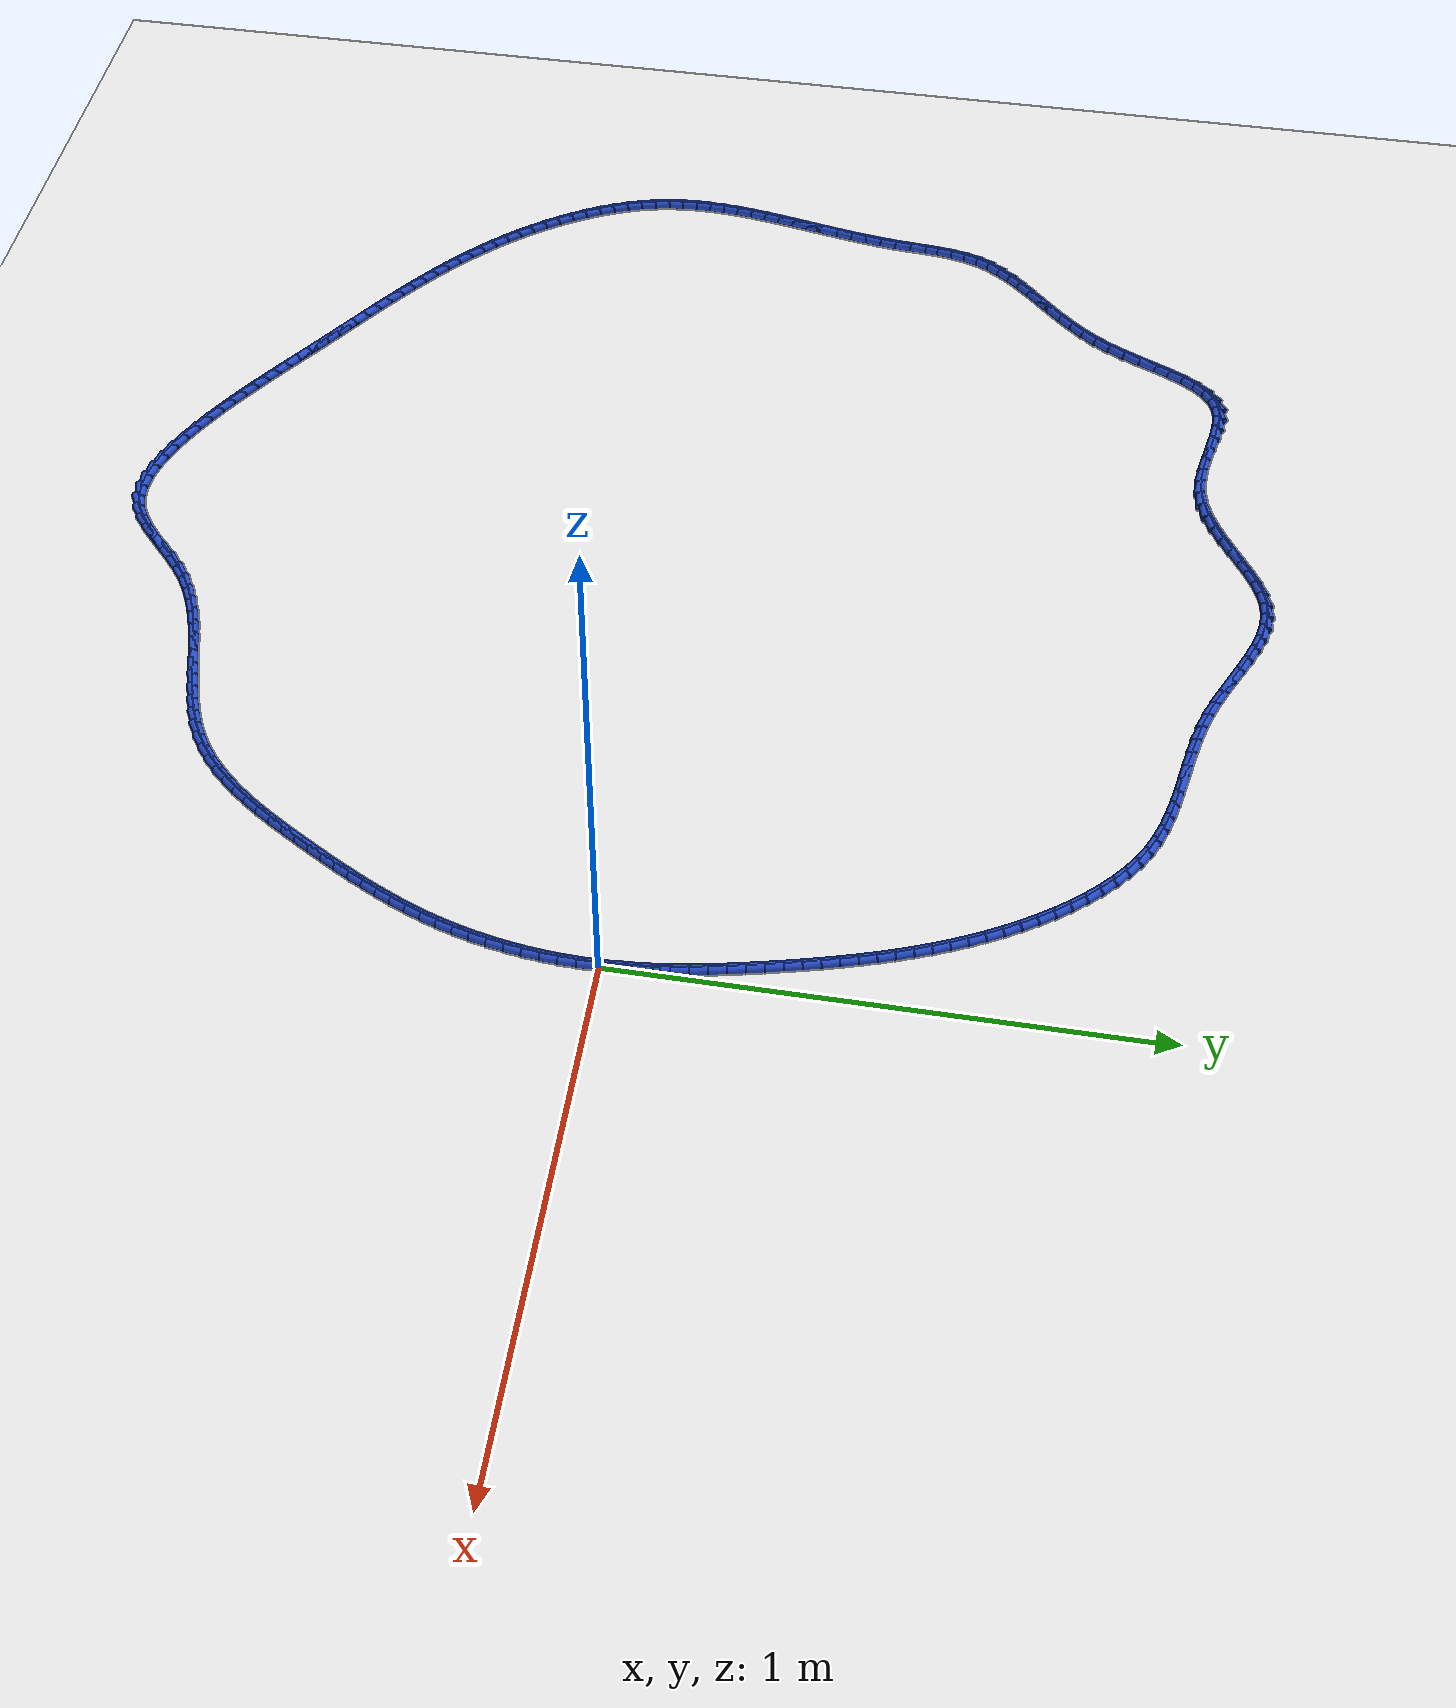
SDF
<sdf version="1.6">
 <world name="default">
  <light name="sun" type="directional">
   <pose>0 0 10 0 -0 0</pose>
   <diffuse>0.8 0.8 0.8 1</diffuse>
   <specular>0.2 0.2 0.2 1</specular>
   <attenuation>
    <range>1000</range>
    <constant>0.9</constant>
    <linear>0.01</linear>
    <quadratic>0.001</quadratic>
   </attenuation>
   <direction>-0.5 0.1 -0.9</direction>
  </light>
  <model name="ground_plane">
   <static>1</static>
   <link name="link">
    <collision name="collision">
     <geometry><plane><normal>0 0 1</normal><size>100 100</size></plane></geometry>
     <surface><friction><ode><mu>100</mu><mu2>50</mu2></ode></friction></surface>
    </collision>
    <visual name="visual">
     <cast_shadows>0</cast_shadows>
     <geometry><plane><normal>0 0 1</normal><size>100 100</size></plane></geometry>
     <material>
      <script><uri>file://media/materials/scripts/gazebo.material</uri><name>Gazebo/WhiteGlow</name></script>
     </material>
    </visual>
   </link>
  </model>
  <gravity>0 0 -9.8</gravity>
  <magnetic_field>6e-06 2.3e-05 -4.2e-05</magnetic_field>
  <atmosphere type="adiabatic"/>
  <physics name="default_physics" default="0" type="ode">
   <max_step_size>0.001</max_step_size>
   <real_time_factor>1</real_time_factor>
   <real_time_update_rate>1000</real_time_update_rate>
  </physics>
  <scene><ambient>0.4 0.4 0.4 1</ambient><background>0.7 0.7 0.7 1</background><shadows>1</shadows></scene>
  <spherical_coordinates>
   <surface_model>EARTH_WGS84</surface_model>
   <latitude_deg>0</latitude_deg>
   <longitude_deg>0</longitude_deg>
   <elevation>0</elevation>
   <heading_deg>0</heading_deg>
  </spherical_coordinates>
  <model name="line">
   <link name="link_0">
    <pose>1.3877787807814457e-17 -2.7755575615628914e-17 0.01 0 1.57 -1.532613430341726</pose>
    <collision name="collision">
     <geometry><cylinder><radius>0.01</radius><length>0.08</length></cylinder></geometry>
    </collision>
    <visual name="visual">
     <material>
      <script><name>Gazebo/Blue</name><uri>file://media/materials/scripts/gazebo.material</uri></script>
     </material>
     <geometry><cylinder><radius>0.01</radius><length>0.08</length></cylinder></geometry>
    </visual>
   </link>
   <link name="link_1">
    <pose>-0.0012398702655292899 0.03245609350188934 0.01 0 1.57 -1.4978906455337775</pose>
    <collision name="collision">
     <geometry><cylinder><radius>0.01</radius><length>0.08</length></cylinder></geometry>
    </collision>
    <visual name="visual">
     <material>
      <script><name>Gazebo/Blue</name><uri>file://media/materials/scripts/gazebo.material</uri></script>
     </material>
     <geometry><cylinder><radius>0.01</radius><length>0.08</length></cylinder></geometry>
    </visual>
   </link>
   <link name="link_2">
    <pose>-0.0036023476428629813 0.0648032321947696 0.01 0 1.57 -1.4662787933861972</pose>
    <collision name="collision">
     <geometry><cylinder><radius>0.01</radius><length>0.08</length></cylinder></geometry>
    </collision>
    <visual name="visual">
     <material>
      <script><name>Gazebo/Blue</name><uri>file://media/materials/scripts/gazebo.material</uri></script>
     </material>
     <geometry><cylinder><radius>0.01</radius><length>0.08</length></cylinder></geometry>
    </visual>
   </link>
   <link name="link_3">
    <pose>-0.006984441857353037 0.09704442551617311 0.01 0 1.57 -1.4378284325319393</pose>
    <collision name="collision">
     <geometry><cylinder><radius>0.01</radius><length>0.08</length></cylinder></geometry>
    </collision>
    <visual name="visual">
     <material>
      <script><name>Gazebo/Blue</name><uri>file://media/materials/scripts/gazebo.material</uri></script>
     </material>
     <geometry><cylinder><radius>0.01</radius><length>0.08</length></cylinder></geometry>
    </visual>
   </link>
   <link name="link_4">
    <pose>-0.011283162634351406 0.12918268290363222 0.01 0 1.57 -1.4125603410802359</pose>
    <collision name="collision">
     <geometry><cylinder><radius>0.01</radius><length>0.08</length></cylinder></geometry>
    </collision>
    <visual name="visual">
     <material>
      <script><name>Gazebo/Blue</name><uri>file://media/materials/scripts/gazebo.material</uri></script>
     </material>
     <geometry><cylinder><radius>0.01</radius><length>0.08</length></cylinder></geometry>
    </visual>
   </link>
   <link name="link_5">
    <pose>-0.01639551969921005 0.16122101379467924 0.01 0 1.57 -1.3904739414616394</pose>
    <collision name="collision">
     <geometry><cylinder><radius>0.01</radius><length>0.08</length></cylinder></geometry>
    </collision>
    <visual name="visual">
     <material>
      <script><name>Gazebo/Blue</name><uri>file://media/materials/scripts/gazebo.material</uri></script>
     </material>
     <geometry><cylinder><radius>0.01</radius><length>0.08</length></cylinder></geometry>
    </visual>
   </link>
   <link name="link_6">
    <pose>-0.022218522777280942 0.19316242762684652 0.01 0 1.57 -1.371554983965618</pose>
    <collision name="collision">
     <geometry><cylinder><radius>0.01</radius><length>0.08</length></cylinder></geometry>
    </collision>
    <visual name="visual">
     <material>
      <script><name>Gazebo/Blue</name><uri>file://media/materials/scripts/gazebo.material</uri></script>
     </material>
     <geometry><cylinder><radius>0.01</radius><length>0.08</length></cylinder></geometry>
    </visual>
   </link>
   <link name="link_7">
    <pose>-0.02864918159391604 0.22500993383766646 0.01 0 1.57 -1.3557822534866633</pose>
    <collision name="collision">
     <geometry><cylinder><radius>0.01</radius><length>0.08</length></cylinder></geometry>
    </collision>
    <visual name="visual">
     <material>
      <script><name>Gazebo/Blue</name><uri>file://media/materials/scripts/gazebo.material</uri></script>
     </material>
     <geometry><cylinder><radius>0.01</radius><length>0.08</length></cylinder></geometry>
    </visual>
   </link>
   <link name="link_8">
    <pose>-0.0355845058744673 0.2567665418646714 0.01 0 1.57 -1.3431332144721129</pose>
    <collision name="collision">
     <geometry><cylinder><radius>0.01</radius><length>0.08</length></cylinder></geometry>
    </collision>
    <visual name="visual">
     <material>
      <script><name>Gazebo/Blue</name><uri>file://media/materials/scripts/gazebo.material</uri></script>
     </material>
     <geometry><cylinder><radius>0.01</radius><length>0.08</length></cylinder></geometry>
    </visual>
   </link>
   <link name="link_9">
    <pose>-0.042921505344286695 0.2884352611453937 0.01 0 1.57 -1.33315017540428</pose>
    <collision name="collision">
     <geometry><cylinder><radius>0.01</radius><length>0.08</length></cylinder></geometry>
    </collision>
    <visual name="visual">
     <material>
      <script><name>Gazebo/Blue</name><uri>file://media/materials/scripts/gazebo.material</uri></script>
     </material>
     <geometry><cylinder><radius>0.01</radius><length>0.08</length></cylinder></geometry>
    </visual>
   </link>
   <link name="link_10">
    <pose>-0.0505713105957971 0.32001688248115157 0.01 0 1.57 -1.3225812194773876</pose>
    <collision name="collision">
     <geometry><cylinder><radius>0.01</radius><length>0.08</length></cylinder></geometry>
    </collision>
    <visual name="visual">
     <material>
      <script><name>Gazebo/Blue</name><uri>file://media/materials/scripts/gazebo.material</uri></script>
     </material>
     <geometry><cylinder><radius>0.01</radius><length>0.08</length></cylinder></geometry>
    </visual>
   </link>
   <link name="link_11">
    <pose>-0.058549376641268885 0.35149580547471015 0.01 0 1.57 -1.3099661245665832</pose>
    <collision name="collision">
     <geometry><cylinder><radius>0.01</radius><length>0.08</length></cylinder></geometry>
    </collision>
    <visual name="visual">
     <material>
      <script><name>Gazebo/Blue</name><uri>file://media/materials/scripts/gazebo.material</uri></script>
     </material>
     <geometry><cylinder><radius>0.01</radius><length>0.08</length></cylinder></geometry>
    </visual>
   </link>
   <link name="link_12">
    <pose>-0.06691790229256095 0.3828490854569823 0.01 0 1.57 -1.2952901988516587</pose>
    <collision name="collision">
     <geometry><cylinder><radius>0.01</radius><length>0.08</length></cylinder></geometry>
    </collision>
    <visual name="visual">
     <material>
      <script><name>Gazebo/Blue</name><uri>file://media/materials/scripts/gazebo.material</uri></script>
     </material>
     <geometry><cylinder><radius>0.01</radius><length>0.08</length></cylinder></geometry>
    </visual>
   </link>
   <link name="link_13">
    <pose>-0.0757393065360075 0.4140537431656045 0.01 0 1.57 -1.2785478756480453</pose>
    <collision name="collision">
     <geometry><cylinder><radius>0.01</radius><length>0.08</length></cylinder></geometry>
    </collision>
    <visual name="visual">
     <material>
      <script><name>Gazebo/Blue</name><uri>file://media/materials/scripts/gazebo.material</uri></script>
     </material>
     <geometry><cylinder><radius>0.01</radius><length>0.08</length></cylinder></geometry>
    </visual>
   </link>
   <link name="link_14">
    <pose>-0.08507600835794266 0.4450867993382128 0.01 0 1.57 -1.2597377585495069</pose>
    <collision name="collision">
     <geometry><cylinder><radius>0.01</radius><length>0.08</length></cylinder></geometry>
    </collision>
    <visual name="visual">
     <material>
      <script><name>Gazebo/Blue</name><uri>file://media/materials/scripts/gazebo.material</uri></script>
     </material>
     <geometry><cylinder><radius>0.01</radius><length>0.08</length></cylinder></geometry>
    </visual>
   </link>
   <link name="link_15">
    <pose>-0.09499042674470057 0.4759252747124434 0.01 0 1.57 -1.2388647729636164</pose>
    <collision name="collision">
     <geometry><cylinder><radius>0.01</radius><length>0.08</length></cylinder></geometry>
    </collision>
    <visual name="visual">
     <material>
      <script><name>Gazebo/Blue</name><uri>file://media/materials/scripts/gazebo.material</uri></script>
     </material>
     <geometry><cylinder><radius>0.01</radius><length>0.08</length></cylinder></geometry>
    </visual>
   </link>
   <link name="link_16">
    <pose>-0.1055449806826154 0.5065461900259327 0.01 0 1.57 -1.215942558549698</pose>
    <collision name="collision">
     <geometry><cylinder><radius>0.01</radius><length>0.08</length></cylinder></geometry>
    </collision>
    <visual name="visual">
     <material>
      <script><name>Gazebo/Blue</name><uri>file://media/materials/scripts/gazebo.material</uri></script>
     </material>
     <geometry><cylinder><radius>0.01</radius><length>0.08</length></cylinder></geometry>
    </visual>
   </link>
   <link name="link_17">
    <pose>-0.11680208915802125 0.5369265660163164 0.01 0 1.57 -1.1909960476434311</pose>
    <collision name="collision">
     <geometry><cylinder><radius>0.01</radius><length>0.08</length></cylinder></geometry>
    </collision>
    <visual name="visual">
     <material>
      <script><name>Gazebo/Blue</name><uri>file://media/materials/scripts/gazebo.material</uri></script>
     </material>
     <geometry><cylinder><radius>0.01</radius><length>0.08</length></cylinder></geometry>
    </visual>
   </link>
   <link name="link_18">
    <pose>-0.12882417115725237 0.5670434234212315 0.01 0 1.57 -1.1640641433164582</pose>
    <collision name="collision">
     <geometry><cylinder><radius>0.01</radius><length>0.08</length></cylinder></geometry>
    </collision>
    <visual name="visual">
     <material>
      <script><name>Gazebo/Blue</name><uri>file://media/materials/scripts/gazebo.material</uri></script>
     </material>
     <geometry><cylinder><radius>0.01</radius><length>0.08</length></cylinder></geometry>
    </visual>
   </link>
   <link name="link_19">
    <pose>-0.14167364566664284 0.5968737829783134 0.01 0 1.57 -1.135202374761682</pose>
    <collision name="collision">
     <geometry><cylinder><radius>0.01</radius><length>0.08</length></cylinder></geometry>
    </collision>
    <visual name="visual">
     <material>
      <script><name>Gazebo/Blue</name><uri>file://media/materials/scripts/gazebo.material</uri></script>
     </material>
     <geometry><cylinder><radius>0.01</radius><length>0.08</length></cylinder></geometry>
    </visual>
   </link>
   <link name="link_20">
    <pose>-0.15541293167252676 0.6263946654251986 0.01 0 1.57 -1.1044853704854731</pose>
    <collision name="collision">
     <geometry><cylinder><radius>0.01</radius><length>0.08</length></cylinder></geometry>
    </collision>
    <visual name="visual">
     <material>
      <script><name>Gazebo/Blue</name><uri>file://media/materials/scripts/gazebo.material</uri></script>
     </material>
     <geometry><cylinder><radius>0.01</radius><length>0.08</length></cylinder></geometry>
    </visual>
   </link>
   <link name="link_21">
    <pose>-0.17010444816123835 0.6555830914995234 0.01 0 1.57 -1.0720089564443716</pose>
    <collision name="collision">
     <geometry><cylinder><radius>0.01</radius><length>0.08</length></cylinder></geometry>
    </collision>
    <visual name="visual">
     <material>
      <script><name>Gazebo/Blue</name><uri>file://media/materials/scripts/gazebo.material</uri></script>
     </material>
     <geometry><cylinder><radius>0.01</radius><length>0.08</length></cylinder></geometry>
    </visual>
   </link>
   <link name="link_22">
    <pose>-0.18581061411911173 0.6844160819389238 0.01 0 1.57 -1.0378916635860012</pose>
    <collision name="collision">
     <geometry><cylinder><radius>0.01</radius><length>0.08</length></cylinder></geometry>
    </collision>
    <visual name="visual">
     <material>
      <script><name>Gazebo/Blue</name><uri>file://media/materials/scripts/gazebo.material</uri></script>
     </material>
     <geometry><cylinder><radius>0.01</radius><length>0.08</length></cylinder></geometry>
    </visual>
   </link>
   <link name="link_23">
    <pose>-0.2025938485324811 0.7128706574810362 0.01 0 1.57 -1.00223773739815</pose>
    <collision name="collision">
     <geometry><cylinder><radius>0.01</radius><length>0.08</length></cylinder></geometry>
    </collision>
    <visual name="visual">
     <material>
      <script><name>Gazebo/Blue</name><uri>file://media/materials/scripts/gazebo.material</uri></script>
     </material>
     <geometry><cylinder><radius>0.01</radius><length>0.08</length></cylinder></geometry>
    </visual>
   </link>
   <link name="link_24">
    <pose>-0.22051532847705393 0.7409195649722435 0.01 0 1.57 -0.9640788097628212</pose>
    <collision name="collision">
     <geometry><cylinder><radius>0.01</radius><length>0.08</length></cylinder></geometry>
    </collision>
    <visual name="visual">
     <material>
      <script><name>Gazebo/Blue</name><uri>file://media/materials/scripts/gazebo.material</uri></script>
     </material>
     <geometry><cylinder><radius>0.01</radius><length>0.08</length></cylinder></geometry>
    </visual>
   </link>
   <link name="link_25">
    <pose>-0.2396032382094972 0.7684220103022011 0.01 0 1.57 -0.9218625431205067</pose>
    <collision name="collision">
     <geometry><cylinder><radius>0.01</radius><length>0.08</length></cylinder></geometry>
    </collision>
    <visual name="visual">
     <material>
      <script><name>Gazebo/Blue</name><uri>file://media/materials/scripts/gazebo.material</uri></script>
     </material>
     <geometry><cylinder><radius>0.01</radius><length>0.08</length></cylinder></geometry>
    </visual>
   </link>
   <link name="link_26">
    <pose>-0.25985010328278485 0.7951144840712775 0.01 0 1.57 -0.874849518328969</pose>
    <collision name="collision">
     <geometry><cylinder><radius>0.01</radius><length>0.08</length></cylinder></geometry>
    </collision>
    <visual name="visual">
     <material>
      <script><name>Gazebo/Blue</name><uri>file://media/materials/scripts/gazebo.material</uri></script>
     </material>
     <geometry><cylinder><radius>0.01</radius><length>0.08</length></cylinder></geometry>
    </visual>
   </link>
   <link name="link_27">
    <pose>-0.281246673152969 0.8207273646484641 0.01 0 1.57 -0.8222749461910553</pose>
    <collision name="collision">
     <geometry><cylinder><radius>0.01</radius><length>0.08</length></cylinder></geometry>
    </collision>
    <visual name="visual">
     <material>
      <script><name>Gazebo/Blue</name><uri>file://media/materials/scripts/gazebo.material</uri></script>
     </material>
     <geometry><cylinder><radius>0.01</radius><length>0.08</length></cylinder></geometry>
    </visual>
   </link>
   <link name="link_28">
    <pose>-0.30378369727610166 0.8449910304027523 0.01 0 1.57 -0.7633043507606859</pose>
    <collision name="collision">
     <geometry><cylinder><radius>0.01</radius><length>0.08</length></cylinder></geometry>
    </collision>
    <visual name="visual">
     <material>
      <script><name>Gazebo/Blue</name><uri>file://media/materials/scripts/gazebo.material</uri></script>
     </material>
     <geometry><cylinder><radius>0.01</radius><length>0.08</length></cylinder></geometry>
    </visual>
   </link>
   <link name="link_29">
    <pose>-0.32745192510823484 0.867635859703133 0.01 0 1.57 -0.6970640896180392</pose>
    <collision name="collision">
     <geometry><cylinder><radius>0.01</radius><length>0.08</length></cylinder></geometry>
    </collision>
    <visual name="visual">
     <material>
      <script><name>Gazebo/Blue</name><uri>file://media/materials/scripts/gazebo.material</uri></script>
     </material>
     <geometry><cylinder><radius>0.01</radius><length>0.08</length></cylinder></geometry>
    </visual>
   </link>
   <link name="link_30">
    <pose>-0.3522421061054208 0.8883922309185982 0.01 0 1.57 -0.6227051639275418</pose>
    <collision name="collision">
     <geometry><cylinder><radius>0.01</radius><length>0.08</length></cylinder></geometry>
    </collision>
    <visual name="visual">
     <material>
      <script><name>Gazebo/Blue</name><uri>file://media/materials/scripts/gazebo.material</uri></script>
     </material>
     <geometry><cylinder><radius>0.01</radius><length>0.08</length></cylinder></geometry>
    </visual>
   </link>
   <link name="link_31">
    <pose>-0.3781449897237109 0.906990522418138 0.01 0 1.57 -0.5395147756456349</pose>
    <collision name="collision">
     <geometry><cylinder><radius>0.01</radius><length>0.08</length></cylinder></geometry>
    </collision>
    <visual name="visual">
     <material>
      <script><name>Gazebo/Blue</name><uri>file://media/materials/scripts/gazebo.material</uri></script>
     </material>
     <geometry><cylinder><radius>0.01</radius><length>0.08</length></cylinder></geometry>
    </visual>
   </link>
   <link name="link_32">
    <pose>-0.40515132541915805 0.923161112570745 0.01 0 1.57 -0.44952952814948094</pose>
    <collision name="collision">
     <geometry><cylinder><radius>0.01</radius><length>0.08</length></cylinder></geometry>
    </collision>
    <visual name="visual">
     <material>
      <script><name>Gazebo/Blue</name><uri>file://media/materials/scripts/gazebo.material</uri></script>
     </material>
     <geometry><cylinder><radius>0.01</radius><length>0.08</length></cylinder></geometry>
    </visual>
   </link>
   <link name="link_33">
    <pose>-0.4332394842948635 0.9367129454690262 0.01 0 1.57 -0.3680498462782511</pose>
    <collision name="collision">
     <geometry><cylinder><radius>0.01</radius><length>0.08</length></cylinder></geometry>
    </collision>
    <visual name="visual">
     <material>
      <script><name>Gazebo/Blue</name><uri>file://media/materials/scripts/gazebo.material</uri></script>
     </material>
     <geometry><cylinder><radius>0.01</radius><length>0.08</length></cylinder></geometry>
    </visual>
   </link>
   <link name="link_34">
    <pose>-0.462313838802202 0.9479246365457925 0.01 0 1.57 -0.3019246639378615</pose>
    <collision name="collision">
     <geometry><cylinder><radius>0.01</radius><length>0.08</length></cylinder></geometry>
    </collision>
    <visual name="visual">
     <material>
      <script><name>Gazebo/Blue</name><uri>file://media/materials/scripts/gazebo.material</uri></script>
     </material>
     <geometry><cylinder><radius>0.01</radius><length>0.08</length></cylinder></geometry>
    </visual>
   </link>
   <link name="link_35">
    <pose>-0.49225138261486673 0.9572485750379284 0.01 0 1.57 -0.2516994135280867</pose>
    <collision name="collision">
     <geometry><cylinder><radius>0.01</radius><length>0.08</length></cylinder></geometry>
    </collision>
    <visual name="visual">
     <material>
      <script><name>Gazebo/Blue</name><uri>file://media/materials/scripts/gazebo.material</uri></script>
     </material>
     <geometry><cylinder><radius>0.01</radius><length>0.08</length></cylinder></geometry>
    </visual>
   </link>
   <link name="link_36">
    <pose>-0.5229290651953346 0.9651374307920357 0.01 0 1.57 -0.21720835206965836</pose>
    <collision name="collision">
     <geometry><cylinder><radius>0.01</radius><length>0.08</length></cylinder></geometry>
    </collision>
    <visual name="visual">
     <material>
      <script><name>Gazebo/Blue</name><uri>file://media/materials/scripts/gazebo.material</uri></script>
     </material>
     <geometry><cylinder><radius>0.01</radius><length>0.08</length></cylinder></geometry>
    </visual>
   </link>
   <link name="link_37">
    <pose>-0.5542238360060833 0.9720438736547168 0.01 0 1.57 -0.19796832872379277</pose>
    <collision name="collision">
     <geometry><cylinder><radius>0.01</radius><length>0.08</length></cylinder></geometry>
    </collision>
    <visual name="visual">
     <material>
      <script><name>Gazebo/Blue</name><uri>file://media/materials/scripts/gazebo.material</uri></script>
     </material>
     <geometry><cylinder><radius>0.01</radius><length>0.08</length></cylinder></geometry>
    </visual>
   </link>
   <link name="link_38">
    <pose>-0.5860126445095902 0.9784205734725735 0.01 0 1.57 -0.1934358672910658</pose>
    <collision name="collision">
     <geometry><cylinder><radius>0.01</radius><length>0.08</length></cylinder></geometry>
    </collision>
    <visual name="visual">
     <material>
      <script><name>Gazebo/Blue</name><uri>file://media/materials/scripts/gazebo.material</uri></script>
     </material>
     <geometry><cylinder><radius>0.01</radius><length>0.08</length></cylinder></geometry>
    </visual>
   </link>
   <link name="link_39">
    <pose>-0.6181724401683326 0.9847202000922074 0.01 0 1.57 -0.20313529746103845</pose>
    <collision name="collision">
     <geometry><cylinder><radius>0.01</radius><length>0.08</length></cylinder></geometry>
    </collision>
    <visual name="visual">
     <material>
      <script><name>Gazebo/Blue</name><uri>file://media/materials/scripts/gazebo.material</uri></script>
     </material>
     <geometry><cylinder><radius>0.01</radius><length>0.08</length></cylinder></geometry>
    </visual>
   </link>
   <link name="link_40">
    <pose>-0.6505801724447882 0.9913954233602211 0.01 0 1.57 -0.22668101221085432</pose>
    <collision name="collision">
     <geometry><cylinder><radius>0.01</radius><length>0.08</length></cylinder></geometry>
    </collision>
    <visual name="visual">
     <material>
      <script><name>Gazebo/Blue</name><uri>file://media/materials/scripts/gazebo.material</uri></script>
     </material>
     <geometry><cylinder><radius>0.01</radius><length>0.08</length></cylinder></geometry>
    </visual>
   </link>
   <link name="link_41">
    <pose>-0.6831127908014344 0.9988989131232164 0.01 0 1.57 -0.26371537399365885</pose>
    <collision name="collision">
     <geometry><cylinder><radius>0.01</radius><length>0.08</length></cylinder></geometry>
    </collision>
    <visual name="visual">
     <material>
      <script><name>Gazebo/Blue</name><uri>file://media/materials/scripts/gazebo.material</uri></script>
     </material>
     <geometry><cylinder><radius>0.01</radius><length>0.08</length></cylinder></geometry>
    </visual>
   </link>
   <link name="link_42">
    <pose>-0.715647244700748 1.007683339227795 0.01 0 1.57 -0.31377782083108036</pose>
    <collision name="collision">
     <geometry><cylinder><radius>0.01</radius><length>0.08</length></cylinder></geometry>
    </collision>
    <visual name="visual">
     <material>
      <script><name>Gazebo/Blue</name><uri>file://media/materials/scripts/gazebo.material</uri></script>
     </material>
     <geometry><cylinder><radius>0.01</radius><length>0.08</length></cylinder></geometry>
    </visual>
   </link>
   <link name="link_43">
    <pose>-0.7480604836052075 1.0182013715205593 0.01 0 1.57 -0.37284487881467715</pose>
    <collision name="collision">
     <geometry><cylinder><radius>0.01</radius><length>0.08</length></cylinder></geometry>
    </collision>
    <visual name="visual">
     <material>
      <script><name>Gazebo/Blue</name><uri>file://media/materials/scripts/gazebo.material</uri></script>
     </material>
     <geometry><cylinder><radius>0.01</radius><length>0.08</length></cylinder></geometry>
    </visual>
   </link>
   <link name="link_44">
    <pose>-0.7802391555915742 1.030787725763193 0.01 0 1.57 -0.4182823193498981</pose>
    <collision name="collision">
     <geometry><cylinder><radius>0.01</radius><length>0.08</length></cylinder></geometry>
    </collision>
    <visual name="visual">
     <material>
      <script><name>Gazebo/Blue</name><uri>file://media/materials/scripts/gazebo.material</uri></script>
     </material>
     <geometry><cylinder><radius>0.01</radius><length>0.08</length></cylinder></geometry>
    </visual>
   </link>
   <link name="link_45">
    <pose>-0.8121365554884025 1.0449665630969243 0.01 0 1.57 -0.44205421708148795</pose>
    <collision name="collision">
     <geometry><cylinder><radius>0.01</radius><length>0.08</length></cylinder></geometry>
    </collision>
    <visual name="visual">
     <material>
      <script><name>Gazebo/Blue</name><uri>file://media/materials/scripts/gazebo.material</uri></script>
     </material>
     <geometry><cylinder><radius>0.01</radius><length>0.08</length></cylinder></geometry>
    </visual>
   </link>
   <link name="link_46">
    <pose>-0.8437339880127642 1.059921389733139 0.01 0 1.57 -0.4448998323377454</pose>
    <collision name="collision">
     <geometry><cylinder><radius>0.01</radius><length>0.08</length></cylinder></geometry>
    </collision>
    <visual name="visual">
     <material>
      <script><name>Gazebo/Blue</name><uri>file://media/materials/scripts/gazebo.material</uri></script>
     </material>
     <geometry><cylinder><radius>0.01</radius><length>0.08</length></cylinder></geometry>
    </visual>
   </link>
   <link name="link_47">
    <pose>-0.8750128546812332 1.0748345346122916 0.01 0 1.57 -0.42634305308882825</pose>
    <collision name="collision">
     <geometry><cylinder><radius>0.01</radius><length>0.08</length></cylinder></geometry>
    </collision>
    <visual name="visual">
     <material>
      <script><name>Gazebo/Blue</name><uri>file://media/materials/scripts/gazebo.material</uri></script>
     </material>
     <geometry><cylinder><radius>0.01</radius><length>0.08</length></cylinder></geometry>
    </visual>
   </link>
   <link name="link_48">
    <pose>-0.9059545570103823 1.0888883266748357 0.01 0 1.57 -0.3845132723790874</pose>
    <collision name="collision">
     <geometry><cylinder><radius>0.01</radius><length>0.08</length></cylinder></geometry>
    </collision>
    <visual name="visual">
     <material>
      <script><name>Gazebo/Blue</name><uri>file://media/materials/scripts/gazebo.material</uri></script>
     </material>
     <geometry><cylinder><radius>0.01</radius><length>0.08</length></cylinder></geometry>
    </visual>
   </link>
   <link name="link_49">
    <pose>-0.9365404965167861 1.1012650948612264 0.01 0 1.57 -0.3161260971678653</pose>
    <collision name="collision">
     <geometry><cylinder><radius>0.01</radius><length>0.08</length></cylinder></geometry>
    </collision>
    <visual name="visual">
     <material>
      <script><name>Gazebo/Blue</name><uri>file://media/materials/scripts/gazebo.material</uri></script>
     </material>
     <geometry><cylinder><radius>0.01</radius><length>0.08</length></cylinder></geometry>
    </visual>
   </link>
   <link name="link_50">
    <pose>-0.9667520747170172 1.1111471681119167 0.01 0 1.57 -0.2168577262575128</pose>
    <collision name="collision">
     <geometry><cylinder><radius>0.01</radius><length>0.08</length></cylinder></geometry>
    </collision>
    <visual name="visual">
     <material>
      <script><name>Gazebo/Blue</name><uri>file://media/materials/scripts/gazebo.material</uri></script>
     </material>
     <geometry><cylinder><radius>0.01</radius><length>0.08</length></cylinder></geometry>
    </visual>
   </link>
   <link name="link_51">
    <pose>-0.99657069312765 1.1177168753673619 0.01 0 1.57 -0.0827725048130366</pose>
    <collision name="collision">
     <geometry><cylinder><radius>0.01</radius><length>0.08</length></cylinder></geometry>
    </collision>
    <visual name="visual">
     <material>
      <script><name>Gazebo/Blue</name><uri>file://media/materials/scripts/gazebo.material</uri></script>
     </material>
     <geometry><cylinder><radius>0.01</radius><length>0.08</length></cylinder></geometry>
    </visual>
   </link>
   <link name="link_52">
    <pose>-1.0259777532652572 1.1201565455680154 0.01 0 1.57 0.08611893550251531</pose>
    <collision name="collision">
     <geometry><cylinder><radius>0.01</radius><length>0.08</length></cylinder></geometry>
    </collision>
    <visual name="visual">
     <material>
      <script><name>Gazebo/Blue</name><uri>file://media/materials/scripts/gazebo.material</uri></script>
     </material>
     <geometry><cylinder><radius>0.01</radius><length>0.08</length></cylinder></geometry>
    </visual>
   </link>
   <link name="link_53">
    <pose>-1.0549552922446777 1.1176548430962816 0.01 0 1.57 0.26071290076999276</pose>
    <collision name="collision">
     <geometry><cylinder><radius>0.01</radius><length>0.08</length></cylinder></geometry>
    </collision>
    <visual name="visual">
     <material>
      <script><name>Gazebo/Blue</name><uri>file://media/materials/scripts/gazebo.material</uri></script>
     </material>
     <geometry><cylinder><radius>0.01</radius><length>0.08</length></cylinder></geometry>
    </visual>
   </link>
   <link name="link_54">
    <pose>-1.083548175945985 1.1100266895430082 0.01 0 1.57 0.3939593451245669</pose>
    <collision name="collision">
     <geometry><cylinder><radius>0.01</radius><length>0.08</length></cylinder></geometry>
    </collision>
    <visual name="visual">
     <material>
      <script><name>Gazebo/Blue</name><uri>file://media/materials/scripts/gazebo.material</uri></script>
     </material>
     <geometry><cylinder><radius>0.01</radius><length>0.08</length></cylinder></geometry>
    </visual>
   </link>
   <link name="link_55">
    <pose>-1.111916370697673 1.0982342912697711 0.01 0 1.57 0.4836126055615789</pose>
    <collision name="collision">
     <geometry><cylinder><radius>0.01</radius><length>0.08</length></cylinder></geometry>
    </collision>
    <visual name="visual">
     <material>
      <script><name>Gazebo/Blue</name><uri>file://media/materials/scripts/gazebo.material</uri></script>
     </material>
     <geometry><cylinder><radius>0.01</radius><length>0.08</length></cylinder></geometry>
    </visual>
   </link>
   <link name="link_56">
    <pose>-1.140232149649637 1.083362525131302 0.01 0 1.57 0.5353586523979912</pose>
    <collision name="collision">
     <geometry><cylinder><radius>0.01</radius><length>0.08</length></cylinder></geometry>
    </collision>
    <visual name="visual">
     <material>
      <script><name>Gazebo/Blue</name><uri>file://media/materials/scripts/gazebo.material</uri></script>
     </material>
     <geometry><cylinder><radius>0.01</radius><length>0.08</length></cylinder></geometry>
    </visual>
   </link>
   <link name="link_57">
    <pose>-1.1686677859517722 1.0664962679823315 0.01 0 1.57 0.5541065408203324</pose>
    <collision name="collision">
     <geometry><cylinder><radius>0.01</radius><length>0.08</length></cylinder></geometry>
    </collision>
    <visual name="visual">
     <material>
      <script><name>Gazebo/Blue</name><uri>file://media/materials/scripts/gazebo.material</uri></script>
     </material>
     <geometry><cylinder><radius>0.01</radius><length>0.08</length></cylinder></geometry>
    </visual>
   </link>
   <link name="link_58">
    <pose>-1.1973955527539744 1.0487203966775922 0.01 0 1.57 0.5425654313970443</pose>
    <collision name="collision">
     <geometry><cylinder><radius>0.01</radius><length>0.08</length></cylinder></geometry>
    </collision>
    <visual name="visual">
     <material>
      <script><name>Gazebo/Blue</name><uri>file://media/materials/scripts/gazebo.material</uri></script>
     </material>
     <geometry><cylinder><radius>0.01</radius><length>0.08</length></cylinder></geometry>
    </visual>
   </link>
   <link name="link_59">
    <pose>-1.2265877232061388 1.0311197880718144 0.01 0 1.57 0.501158423794729</pose>
    <collision name="collision">
     <geometry><cylinder><radius>0.01</radius><length>0.08</length></cylinder></geometry>
    </collision>
    <visual name="visual">
     <material>
      <script><name>Gazebo/Blue</name><uri>file://media/materials/scripts/gazebo.material</uri></script>
     </material>
     <geometry><cylinder><radius>0.01</radius><length>0.08</length></cylinder></geometry>
    </visual>
   </link>
   <link name="link_60">
    <pose>-1.2564165704581611 1.0147793190197296 0.01 0 1.57 0.4284972848036005</pose>
    <collision name="collision">
     <geometry><cylinder><radius>0.01</radius><length>0.08</length></cylinder></geometry>
    </collision>
    <visual name="visual">
     <material>
      <script><name>Gazebo/Blue</name><uri>file://media/materials/scripts/gazebo.material</uri></script>
     </material>
     <geometry><cylinder><radius>0.01</radius><length>0.08</length></cylinder></geometry>
    </visual>
   </link>
   <link name="link_61">
    <pose>-1.2870543676599366 1.00078386637607 0.01 0 1.57 0.3224871878234295</pose>
    <collision name="collision">
     <geometry><cylinder><radius>0.01</radius><length>0.08</length></cylinder></geometry>
    </collision>
    <visual name="visual">
     <material>
      <script><name>Gazebo/Blue</name><uri>file://media/materials/scripts/gazebo.material</uri></script>
     </material>
     <geometry><cylinder><radius>0.01</radius><length>0.08</length></cylinder></geometry>
    </visual>
   </link>
   <link name="link_62">
    <pose>-1.3186733879613601 0.9902183069955662 0.01 0 1.57 0.1825742327631853</pose>
    <collision name="collision">
     <geometry><cylinder><radius>0.01</radius><length>0.08</length></cylinder></geometry>
    </collision>
    <visual name="visual">
     <material>
      <script><name>Gazebo/Blue</name><uri>file://media/materials/scripts/gazebo.material</uri></script>
     </material>
     <geometry><cylinder><radius>0.01</radius><length>0.08</length></cylinder></geometry>
    </visual>
   </link>
   <link name="link_63">
    <pose>-1.3514459021469807 0.9841675093646113 0.01 0 1.57 0.02684532839024324</pose>
    <collision name="collision">
     <geometry><cylinder><radius>0.01</radius><length>0.08</length></cylinder></geometry>
    </collision>
    <visual name="visual">
     <material>
      <script><name>Gazebo/Blue</name><uri>file://media/materials/scripts/gazebo.material</uri></script>
     </material>
     <geometry><cylinder><radius>0.01</radius><length>0.08</length></cylinder></geometry>
    </visual>
   </link>
   <link name="link_64">
    <pose>-1.3854138960708653 0.983255408293976 0.01 0 1.57 -0.09046818717673741</pose>
    <collision name="collision">
     <geometry><cylinder><radius>0.01</radius><length>0.08</length></cylinder></geometry>
    </collision>
    <visual name="visual">
     <material>
      <script><name>Gazebo/Blue</name><uri>file://media/materials/scripts/gazebo.material</uri></script>
     </material>
     <geometry><cylinder><radius>0.01</radius><length>0.08</length></cylinder></geometry>
    </visual>
   </link>
   <link name="link_65">
    <pose>-1.420138718775987 0.9864054987111578 0.01 0 1.57 -0.16296738304080768</pose>
    <collision name="collision">
     <geometry><cylinder><radius>0.01</radius><length>0.08</length></cylinder></geometry>
    </collision>
    <visual name="visual">
     <material>
      <script><name>Gazebo/Blue</name><uri>file://media/materials/scripts/gazebo.material</uri></script>
     </material>
     <geometry><cylinder><radius>0.01</radius><length>0.08</length></cylinder></geometry>
    </visual>
   </link>
   <link name="link_66">
    <pose>-1.4550709101351507 0.9921492449541518 0.01 0 1.57 -0.19602881218156004</pose>
    <collision name="collision">
     <geometry><cylinder><radius>0.01</radius><length>0.08</length></cylinder></geometry>
    </collision>
    <visual name="visual">
     <material>
      <script><name>Gazebo/Blue</name><uri>file://media/materials/scripts/gazebo.material</uri></script>
     </material>
     <geometry><cylinder><radius>0.01</radius><length>0.08</length></cylinder></geometry>
    </visual>
   </link>
   <link name="link_67">
    <pose>-1.4896610100211571 0.9990181113609515 0.01 0 1.57 -0.19127459408507944</pose>
    <collision name="collision">
     <geometry><cylinder><radius>0.01</radius><length>0.08</length></cylinder></geometry>
    </collision>
    <visual name="visual">
     <material>
      <script><name>Gazebo/Blue</name><uri>file://media/materials/scripts/gazebo.material</uri></script>
     </material>
     <geometry><cylinder><radius>0.01</radius><length>0.08</length></cylinder></geometry>
    </visual>
   </link>
   <link name="link_68">
    <pose>-1.52335955830681 1.0055435622695512 0.01 0 1.57 -0.14509404896703468</pose>
    <collision name="collision">
     <geometry><cylinder><radius>0.01</radius><length>0.08</length></cylinder></geometry>
    </collision>
    <visual name="visual">
     <material>
      <script><name>Gazebo/Blue</name><uri>file://media/materials/scripts/gazebo.material</uri></script>
     </material>
     <geometry><cylinder><radius>0.01</radius><length>0.08</length></cylinder></geometry>
    </visual>
   </link>
   <link name="link_69">
    <pose>-1.5556170948649124 1.010257062017945 0.01 0 1.57 -0.04731029014906379</pose>
    <collision name="collision">
     <geometry><cylinder><radius>0.01</radius><length>0.08</length></cylinder></geometry>
    </collision>
    <visual name="visual">
     <material>
      <script><name>Gazebo/Blue</name><uri>file://media/materials/scripts/gazebo.material</uri></script>
     </material>
     <geometry><cylinder><radius>0.01</radius><length>0.08</length></cylinder></geometry>
    </visual>
   </link>
   <link name="link_70">
    <pose>-1.5858841595682664 1.0116900749441267 0.01 0 1.57 0.11902905592434371</pose>
    <collision name="collision">
     <geometry><cylinder><radius>0.01</radius><length>0.08</length></cylinder></geometry>
    </collision>
    <visual name="visual">
     <material>
      <script><name>Gazebo/Blue</name><uri>file://media/materials/scripts/gazebo.material</uri></script>
     </material>
     <geometry><cylinder><radius>0.01</radius><length>0.08</length></cylinder></geometry>
    </visual>
   </link>
   <link name="link_71">
    <pose>-1.6136112922896761 1.0083740653860909 0.01 0 1.57 0.3674107815482375</pose>
    <collision name="collision">
     <geometry><cylinder><radius>0.01</radius><length>0.08</length></cylinder></geometry>
    </collision>
    <visual name="visual">
     <material>
      <script><name>Gazebo/Blue</name><uri>file://media/materials/scripts/gazebo.material</uri></script>
     </material>
     <geometry><cylinder><radius>0.01</radius><length>0.08</length></cylinder></geometry>
    </visual>
   </link>
   <link name="link_72">
    <pose>-1.6382690138259495 0.9988836188424973 0.01 0 1.57 0.6358802959516996</pose>
    <collision name="collision">
     <geometry><cylinder><radius>0.01</radius><length>0.08</length></cylinder></geometry>
    </collision>
    <visual name="visual">
     <material>
      <script><name>Gazebo/Blue</name><uri>file://media/materials/scripts/gazebo.material</uri></script>
     </material>
     <geometry><cylinder><radius>0.01</radius><length>0.08</length></cylinder></geometry>
    </visual>
   </link>
   <link name="link_73">
    <pose>-1.6598614656077455 0.9829449362768021 0.01 0 1.57 0.8421692727875335</pose>
    <collision name="collision">
     <geometry><cylinder><radius>0.01</radius><length>0.08</length></cylinder></geometry>
    </collision>
    <visual name="visual">
     <material>
      <script><name>Gazebo/Blue</name><uri>file://media/materials/scripts/gazebo.material</uri></script>
     </material>
     <geometry><cylinder><radius>0.01</radius><length>0.08</length></cylinder></geometry>
    </visual>
   </link>
   <link name="link_74">
    <pose>-1.6789711164593724 0.961532316510751 0.01 0 1.57 0.9826582650933804</pose>
    <collision name="collision">
     <geometry><cylinder><radius>0.01</radius><length>0.08</length></cylinder></geometry>
    </collision>
    <visual name="visual">
     <material>
      <script><name>Gazebo/Blue</name><uri>file://media/materials/scripts/gazebo.material</uri></script>
     </material>
     <geometry><cylinder><radius>0.01</radius><length>0.08</length></cylinder></geometry>
    </visual>
   </link>
   <link name="link_75">
    <pose>-1.6962093756284415 0.9356825151695124 0.01 0 1.57 1.070827798326646</pose>
    <collision name="collision">
     <geometry><cylinder><radius>0.01</radius><length>0.08</length></cylinder></geometry>
    </collision>
    <visual name="visual">
     <material>
      <script><name>Gazebo/Blue</name><uri>file://media/materials/scripts/gazebo.material</uri></script>
     </material>
     <geometry><cylinder><radius>0.01</radius><length>0.08</length></cylinder></geometry>
    </visual>
   </link>
   <link name="link_76">
    <pose>-1.712187652362564 0.906432287878255 0.01 0 1.57 1.1192983352306827</pose>
    <collision name="collision">
     <geometry><cylinder><radius>0.01</radius><length>0.08</length></cylinder></geometry>
    </collision>
    <visual name="visual">
     <material>
      <script><name>Gazebo/Blue</name><uri>file://media/materials/scripts/gazebo.material</uri></script>
     </material>
     <geometry><cylinder><radius>0.01</radius><length>0.08</length></cylinder></geometry>
    </visual>
   </link>
   <link name="link_77">
    <pose>-1.7275173559093489 0.8748183902621482 0.01 0 1.57 1.1361612998513244</pose>
    <collision name="collision">
     <geometry><cylinder><radius>0.01</radius><length>0.08</length></cylinder></geometry>
    </collision>
    <visual name="visual">
     <material>
      <script><name>Gazebo/Blue</name><uri>file://media/materials/scripts/gazebo.material</uri></script>
     </material>
     <geometry><cylinder><radius>0.01</radius><length>0.08</length></cylinder></geometry>
    </visual>
   </link>
   <link name="link_78">
    <pose>-1.7428098955164075 0.8418775779463604 0.01 0 1.57 1.1253347935233187</pose>
    <collision name="collision">
     <geometry><cylinder><radius>0.01</radius><length>0.08</length></cylinder></geometry>
    </collision>
    <visual name="visual">
     <material>
      <script><name>Gazebo/Blue</name><uri>file://media/materials/scripts/gazebo.material</uri></script>
     </material>
     <geometry><cylinder><radius>0.01</radius><length>0.08</length></cylinder></geometry>
    </visual>
   </link>
   <link name="link_79">
    <pose>-1.7586766804313507 0.8086466065560602 0.01 0 1.57 1.0873941480818492</pose>
    <collision name="collision">
     <geometry><cylinder><radius>0.01</radius><length>0.08</length></cylinder></geometry>
    </collision>
    <visual name="visual">
     <material>
      <script><name>Gazebo/Blue</name><uri>file://media/materials/scripts/gazebo.material</uri></script>
     </material>
     <geometry><cylinder><radius>0.01</radius><length>0.08</length></cylinder></geometry>
    </visual>
   </link>
   <link name="link_80">
    <pose>-1.7757291199017877 0.776162231716417 0.01 0 1.57 1.020700433707842</pose>
    <collision name="collision">
     <geometry><cylinder><radius>0.01</radius><length>0.08</length></cylinder></geometry>
    </collision>
    <visual name="visual">
     <material>
      <script><name>Gazebo/Blue</name><uri>file://media/materials/scripts/gazebo.material</uri></script>
     </material>
     <geometry><cylinder><radius>0.01</radius><length>0.08</length></cylinder></geometry>
    </visual>
   </link>
   <link name="link_81">
    <pose>-1.7945660336214473 0.7454450558118114 0.01 0 1.57 0.9417394753219249</pose>
    <collision name="collision">
     <geometry><cylinder><radius>0.01</radius><length>0.08</length></cylinder></geometry>
    </collision>
    <visual name="visual">
     <material>
      <script><name>Gazebo/Blue</name><uri>file://media/materials/scripts/gazebo.material</uri></script>
     </material>
     <geometry><cylinder><radius>0.01</radius><length>0.08</length></cylinder></geometry>
    </visual>
   </link>
   <link name="link_82">
    <pose>-1.8153224520290088 0.7169206085512071 0.01 0 1.57 0.8759331769046607</pose>
    <collision name="collision">
     <geometry><cylinder><radius>0.01</radius><length>0.08</length></cylinder></geometry>
    </collision>
    <visual name="visual">
     <material>
      <script><name>Gazebo/Blue</name><uri>file://media/materials/scripts/gazebo.material</uri></script>
     </material>
     <geometry><cylinder><radius>0.01</radius><length>0.08</length></cylinder></geometry>
    </visual>
   </link>
   <link name="link_83">
    <pose>-1.8375453484429471 0.6902599029746055 0.01 0 1.57 0.8262265913954441</pose>
    <collision name="collision">
     <geometry><cylinder><radius>0.01</radius><length>0.08</length></cylinder></geometry>
    </collision>
    <visual name="visual">
     <material>
      <script><name>Gazebo/Blue</name><uri>file://media/materials/scripts/gazebo.material</uri></script>
     </material>
     <geometry><cylinder><radius>0.01</radius><length>0.08</length></cylinder></geometry>
    </visual>
   </link>
   <link name="link_84">
    <pose>-1.8607438131591152 0.6650853456668587 0.01 0 1.57 0.7934165496593453</pose>
    <collision name="collision">
     <geometry><cylinder><radius>0.01</radius><length>0.08</length></cylinder></geometry>
    </collision>
    <visual name="visual">
     <material>
      <script><name>Gazebo/Blue</name><uri>file://media/materials/scripts/gazebo.material</uri></script>
     </material>
     <geometry><cylinder><radius>0.01</radius><length>0.08</length></cylinder></geometry>
    </visual>
   </link>
   <link name="link_85">
    <pose>-1.8844269364733663 0.6410193432128177 0.01 0 1.57 0.7781271304767212</pose>
    <collision name="collision">
     <geometry><cylinder><radius>0.01</radius><length>0.08</length></cylinder></geometry>
    </collision>
    <visual name="visual">
     <material>
      <script><name>Gazebo/Blue</name><uri>file://media/materials/scripts/gazebo.material</uri></script>
     </material>
     <geometry><cylinder><radius>0.01</radius><length>0.08</length></cylinder></geometry>
    </visual>
   </link>
   <link name="link_86">
    <pose>-1.9081038086815538 0.6176843021973352 0.01 0 1.57 0.781108058290066</pose>
    <collision name="collision">
     <geometry><cylinder><radius>0.01</radius><length>0.08</length></cylinder></geometry>
    </collision>
    <visual name="visual">
     <material>
      <script><name>Gazebo/Blue</name><uri>file://media/materials/scripts/gazebo.material</uri></script>
     </material>
     <geometry><cylinder><radius>0.01</radius><length>0.08</length></cylinder></geometry>
    </visual>
   </link>
   <link name="link_87">
    <pose>-1.93128352007953 0.5947026292052618 0.01 0 1.57 0.80341174198927</pose>
    <collision name="collision">
     <geometry><cylinder><radius>0.01</radius><length>0.08</length></cylinder></geometry>
    </collision>
    <visual name="visual">
     <material>
      <script><name>Gazebo/Blue</name><uri>file://media/materials/scripts/gazebo.material</uri></script>
     </material>
     <geometry><cylinder><radius>0.01</radius><length>0.08</length></cylinder></geometry>
    </visual>
   </link>
   <link name="link_88">
    <pose>-1.9534751609631484 0.5716967308214496 0.01 0 1.57 0.8464065260040293</pose>
    <collision name="collision">
     <geometry><cylinder><radius>0.01</radius><length>0.08</length></cylinder></geometry>
    </collision>
    <visual name="visual">
     <material>
      <script><name>Gazebo/Blue</name><uri>file://media/materials/scripts/gazebo.material</uri></script>
     </material>
     <geometry><cylinder><radius>0.01</radius><length>0.08</length></cylinder></geometry>
    </visual>
   </link>
   <link name="link_89">
    <pose>-1.9741878216282622 0.5482890136307508 0.01 0 1.57 0.9115444964029439</pose>
    <collision name="collision">
     <geometry><cylinder><radius>0.01</radius><length>0.08</length></cylinder></geometry>
    </collision>
    <visual name="visual">
     <material>
      <script><name>Gazebo/Blue</name><uri>file://media/materials/scripts/gazebo.material</uri></script>
     </material>
     <geometry><cylinder><radius>0.01</radius><length>0.08</length></cylinder></geometry>
    </visual>
   </link>
   <link name="link_90">
    <pose>-1.9929305923707248 0.5241018842180165 0.01 0 1.57 0.9997572774891038</pose>
    <collision name="collision">
     <geometry><cylinder><radius>0.01</radius><length>0.08</length></cylinder></geometry>
    </collision>
    <visual name="visual">
     <material>
      <script><name>Gazebo/Blue</name><uri>file://media/materials/scripts/gazebo.material</uri></script>
     </material>
     <geometry><cylinder><radius>0.01</radius><length>0.08</length></cylinder></geometry>
    </visual>
   </link>
   <link name="link_91">
    <pose>-2.0092125634863893 0.4987577491680988 0.01 0 1.57 1.1104013209650891</pose>
    <collision name="collision">
     <geometry><cylinder><radius>0.01</radius><length>0.08</length></cylinder></geometry>
    </collision>
    <visual name="visual">
     <material>
      <script><name>Gazebo/Blue</name><uri>file://media/materials/scripts/gazebo.material</uri></script>
     </material>
     <geometry><cylinder><radius>0.01</radius><length>0.08</length></cylinder></geometry>
    </visual>
   </link>
   <link name="link_92">
    <pose>-2.022542825271108 0.4718790150658488 0.01 0 1.57 1.23686422084998</pose>
    <collision name="collision">
     <geometry><cylinder><radius>0.01</radius><length>0.08</length></cylinder></geometry>
    </collision>
    <visual name="visual">
     <material>
      <script><name>Gazebo/Blue</name><uri>file://media/materials/scripts/gazebo.material</uri></script>
     </material>
     <geometry><cylinder><radius>0.01</radius><length>0.08</length></cylinder></geometry>
    </visual>
   </link>
   <link name="link_93">
    <pose>-2.0325142716973437 0.4431365836718607 0.01 0 1.57 1.345286339407947</pose>
    <collision name="collision">
     <geometry><cylinder><radius>0.01</radius><length>0.08</length></cylinder></geometry>
    </collision>
    <visual name="visual">
     <material>
      <script><name>Gazebo/Blue</name><uri>file://media/materials/scripts/gazebo.material</uri></script>
     </material>
     <geometry><cylinder><radius>0.01</radius><length>0.08</length></cylinder></geometry>
    </visual>
   </link>
   <link name="link_94">
    <pose>-2.0395067199440184 0.41265673031429295 0.01 0 1.57 1.420433913080323</pose>
    <collision name="collision">
     <geometry><cylinder><radius>0.01</radius><length>0.08</length></cylinder></geometry>
    </collision>
    <visual name="visual">
     <material>
      <script><name>Gazebo/Blue</name><uri>file://media/materials/scripts/gazebo.material</uri></script>
     </material>
     <geometry><cylinder><radius>0.01</radius><length>0.08</length></cylinder></geometry>
    </visual>
   </link>
   <link name="link_95">
    <pose>-2.0443309159976875 0.3808150984767818 0.01 0 1.57 1.4654430546764294</pose>
    <collision name="collision">
     <geometry><cylinder><radius>0.01</radius><length>0.08</length></cylinder></geometry>
    </collision>
    <visual name="visual">
     <material>
      <script><name>Gazebo/Blue</name><uri>file://media/materials/scripts/gazebo.material</uri></script>
     </material>
     <geometry><cylinder><radius>0.01</radius><length>0.08</length></cylinder></geometry>
    </visual>
   </link>
   <link name="link_96">
    <pose>-2.047802011809669 0.3479898812689988 0.01 0 1.57 1.483282049844301</pose>
    <collision name="collision">
     <geometry><cylinder><radius>0.01</radius><length>0.08</length></cylinder></geometry>
    </collision>
    <visual name="visual">
     <material>
      <script><name>Gazebo/Blue</name><uri>file://media/materials/scripts/gazebo.material</uri></script>
     </material>
     <geometry><cylinder><radius>0.01</radius><length>0.08</length></cylinder></geometry>
    </visual>
   </link>
   <link name="link_97">
    <pose>-2.050735159331285 0.31455927180061494 0.01 0 1.57 1.4757019498879642</pose>
    <collision name="collision">
     <geometry><cylinder><radius>0.01</radius><length>0.08</length></cylinder></geometry>
    </collision>
    <visual name="visual">
     <material>
      <script><name>Gazebo/Blue</name><uri>file://media/materials/scripts/gazebo.material</uri></script>
     </material>
     <geometry><cylinder><radius>0.01</radius><length>0.08</length></cylinder></geometry>
    </visual>
   </link>
   <link name="link_98">
    <pose>-2.0539455105138558 0.28090146318130066 0.01 0 1.57 1.4476757739323505</pose>
    <collision name="collision">
     <geometry><cylinder><radius>0.01</radius><length>0.08</length></cylinder></geometry>
    </collision>
    <visual name="visual">
     <material>
      <script><name>Gazebo/Blue</name><uri>file://media/materials/scripts/gazebo.material</uri></script>
     </material>
     <geometry><cylinder><radius>0.01</radius><length>0.08</length></cylinder></geometry>
    </visual>
   </link>
   <link name="link_99">
    <pose>-2.0580987008788947 0.2473393696405093 0.01 0 1.57 1.419792785299064</pose>
    <collision name="collision">
     <geometry><cylinder><radius>0.01</radius><length>0.08</length></cylinder></geometry>
    </collision>
    <visual name="visual">
     <material>
      <script><name>Gazebo/Blue</name><uri>file://media/materials/scripts/gazebo.material</uri></script>
     </material>
     <geometry><cylinder><radius>0.01</radius><length>0.08</length></cylinder></geometry>
    </visual>
   </link>
   <link name="link_100">
    <pose>-2.0631801388192175 0.2139444133541593 0.01 0 1.57 1.397934028483175</pose>
    <collision name="collision">
     <geometry><cylinder><radius>0.01</radius><length>0.08</length></cylinder></geometry>
    </collision>
    <visual name="visual">
     <material>
      <script><name>Gazebo/Blue</name><uri>file://media/materials/scripts/gazebo.material</uri></script>
     </material>
     <geometry><cylinder><radius>0.01</radius><length>0.08</length></cylinder></geometry>
    </visual>
   </link>
   <link name="link_101">
    <pose>-2.068981889919397 0.18071653422727982 0.01 0 1.57 1.3820842591566451</pose>
    <collision name="collision">
     <geometry><cylinder><radius>0.01</radius><length>0.08</length></cylinder></geometry>
    </collision>
    <visual name="visual">
     <material>
      <script><name>Gazebo/Blue</name><uri>file://media/materials/scripts/gazebo.material</uri></script>
     </material>
     <geometry><cylinder><radius>0.01</radius><length>0.08</length></cylinder></geometry>
    </visual>
   </link>
   <link name="link_102">
    <pose>-2.075296006335812 0.14765566720025844 0.01 0 1.57 1.372239088665387</pose>
    <collision name="collision">
     <geometry><cylinder><radius>0.01</radius><length>0.08</length></cylinder></geometry>
    </collision>
    <visual name="visual">
     <material>
      <script><name>Gazebo/Blue</name><uri>file://media/materials/scripts/gazebo.material</uri></script>
     </material>
     <geometry><cylinder><radius>0.01</radius><length>0.08</length></cylinder></geometry>
    </visual>
   </link>
   <link name="link_103">
    <pose>-2.081914540224841 0.11476174721348167 0.01 0 1.57 1.368422947065007</pose>
    <collision name="collision">
     <geometry><cylinder><radius>0.01</radius><length>0.08</length></cylinder></geometry>
    </collision>
    <visual name="visual">
     <material>
      <script><name>Gazebo/Blue</name><uri>file://media/materials/scripts/gazebo.material</uri></script>
     </material>
     <geometry><cylinder><radius>0.01</radius><length>0.08</length></cylinder></geometry>
    </visual>
   </link>
   <link name="link_104">
    <pose>-2.088629543742863 0.08203470920733646 0.01 0 1.57 1.3707006971871254</pose>
    <collision name="collision">
     <geometry><cylinder><radius>0.01</radius><length>0.08</length></cylinder></geometry>
    </collision>
    <visual name="visual">
     <material>
      <script><name>Gazebo/Blue</name><uri>file://media/materials/scripts/gazebo.material</uri></script>
     </material>
     <geometry><cylinder><radius>0.01</radius><length>0.08</length></cylinder></geometry>
    </visual>
   </link>
   <link name="link_105">
    <pose>-2.0952330690462544 0.04947448812220973 0.01 0 1.57 1.379183553240131</pose>
    <collision name="collision">
     <geometry><cylinder><radius>0.01</radius><length>0.08</length></cylinder></geometry>
    </collision>
    <visual name="visual">
     <material>
      <script><name>Gazebo/Blue</name><uri>file://media/materials/scripts/gazebo.material</uri></script>
     </material>
     <geometry><cylinder><radius>0.01</radius><length>0.08</length></cylinder></geometry>
    </visual>
   </link>
   <link name="link_106">
    <pose>-2.1015171682913962 0.017081018898487618 0.01 0 1.57 1.3940290499937653</pose>
    <collision name="collision">
     <geometry><cylinder><radius>0.01</radius><length>0.08</length></cylinder></geometry>
    </collision>
    <visual name="visual">
     <material>
      <script><name>Gazebo/Blue</name><uri>file://media/materials/scripts/gazebo.material</uri></script>
     </material>
     <geometry><cylinder><radius>0.01</radius><length>0.08</length></cylinder></geometry>
    </visual>
   </link>
   <link name="link_107">
    <pose>-2.1072738936346656 -0.01514576352344139 0.01 0 1.57 1.4154341234439043</pose>
    <collision name="collision">
     <geometry><cylinder><radius>0.01</radius><length>0.08</length></cylinder></geometry>
    </collision>
    <visual name="visual">
     <material>
      <script><name>Gazebo/Blue</name><uri>file://media/materials/scripts/gazebo.material</uri></script>
     </material>
     <geometry><cylinder><radius>0.01</radius><length>0.08</length></cylinder></geometry>
    </visual>
   </link>
   <link name="link_108">
    <pose>-2.1122952972324414 -0.047205924203191245 0.01 0 1.57 1.443619611413756</pose>
    <collision name="collision">
     <geometry><cylinder><radius>0.01</radius><length>0.08</length></cylinder></geometry>
    </collision>
    <visual name="visual">
     <material>
      <script><name>Gazebo/Blue</name><uri>file://media/materials/scripts/gazebo.material</uri></script>
     </material>
     <geometry><cylinder><radius>0.01</radius><length>0.08</length></cylinder></geometry>
    </visual>
   </link>
   <link name="link_109">
    <pose>-2.1163734312411018 -0.0790995282003749 0.01 0 1.57 1.4788038560043302</pose>
    <collision name="collision">
     <geometry><cylinder><radius>0.01</radius><length>0.08</length></cylinder></geometry>
    </collision>
    <visual name="visual">
     <material>
      <script><name>Gazebo/Blue</name><uri>file://media/materials/scripts/gazebo.material</uri></script>
     </material>
     <geometry><cylinder><radius>0.01</radius><length>0.08</length></cylinder></geometry>
    </visual>
   </link>
   <link name="link_110">
    <pose>-2.1193003478170245 -0.11082664057460553 0.01 0 1.57 1.5211629402948066</pose>
    <collision name="collision">
     <geometry><cylinder><radius>0.01</radius><length>0.08</length></cylinder></geometry>
    </collision>
    <visual name="visual">
     <material>
      <script><name>Gazebo/Blue</name><uri>file://media/materials/scripts/gazebo.material</uri></script>
     </material>
     <geometry><cylinder><radius>0.01</radius><length>0.08</length></cylinder></geometry>
    </visual>
   </link>
   <link name="link_111">
    <pose>-2.120868099116589 -0.1423873263854962 0.01 0 1.57 1.5707759989299488</pose>
    <collision name="collision">
     <geometry><cylinder><radius>0.01</radius><length>0.08</length></cylinder></geometry>
    </collision>
    <visual name="visual">
     <material>
      <script><name>Gazebo/Blue</name><uri>file://media/materials/scripts/gazebo.material</uri></script>
     </material>
     <geometry><cylinder><radius>0.01</radius><length>0.08</length></cylinder></geometry>
    </visual>
   </link>
   <link name="link_112">
    <pose>-2.1208687372961736 -0.17378165069266072 0.01 0 1.57 -1.514035880659315</pose>
    <collision name="collision">
     <geometry><cylinder><radius>0.01</radius><length>0.08</length></cylinder></geometry>
    </collision>
    <visual name="visual">
     <material>
      <script><name>Gazebo/Blue</name><uri>file://media/materials/scripts/gazebo.material</uri></script>
     </material>
     <geometry><cylinder><radius>0.01</radius><length>0.08</length></cylinder></geometry>
    </visual>
   </link>
   <link name="link_113">
    <pose>-2.1190943145121564 -0.20500967855571067 0.01 0 1.57 -1.4504148954085696</pose>
    <collision name="collision">
     <geometry><cylinder><radius>0.01</radius><length>0.08</length></cylinder></geometry>
    </collision>
    <visual name="visual">
     <material>
      <script><name>Gazebo/Blue</name><uri>file://media/materials/scripts/gazebo.material</uri></script>
     </material>
     <geometry><cylinder><radius>0.01</radius><length>0.08</length></cylinder></geometry>
    </visual>
   </link>
   <link name="link_114">
    <pose>-2.1153368829209165 -0.23607147503425996 0.01 0 1.57 -1.3805933088561524</pose>
    <collision name="collision">
     <geometry><cylinder><radius>0.01</radius><length>0.08</length></cylinder></geometry>
    </collision>
    <visual name="visual">
     <material>
      <script><name>Gazebo/Blue</name><uri>file://media/materials/scripts/gazebo.material</uri></script>
     </material>
     <geometry><cylinder><radius>0.01</radius><length>0.08</length></cylinder></geometry>
    </visual>
   </link>
   <link name="link_115">
    <pose>-2.109388537775367 -0.2669670945738823 0.01 0 1.57 -1.3080443837125162</pose>
    <collision name="collision">
     <geometry><cylinder><radius>0.01</radius><length>0.08</length></cylinder></geometry>
    </collision>
    <visual name="visual">
     <material>
      <script><name>Gazebo/Blue</name><uri>file://media/materials/scripts/gazebo.material</uri></script>
     </material>
     <geometry><cylinder><radius>0.01</radius><length>0.08</length></cylinder></geometry>
    </visual>
   </link>
   <link name="link_116">
    <pose>-2.1011290185455165 -0.2976750061454628 0.01 0 1.57 -1.2409234858547042</pose>
    <collision name="collision">
     <geometry><cylinder><radius>0.01</radius><length>0.08</length></cylinder></geometry>
    </collision>
    <visual name="visual">
     <material>
      <script><name>Gazebo/Blue</name><uri>file://media/materials/scripts/gazebo.material</uri></script>
     </material>
     <geometry><cylinder><radius>0.01</radius><length>0.08</length></cylinder></geometry>
    </visual>
   </link>
   <link name="link_117">
    <pose>-2.0907097033669713 -0.3281067781332328 0.01 0 1.57 -1.1801900179687543</pose>
    <collision name="collision">
     <geometry><cylinder><radius>0.01</radius><length>0.08</length></cylinder></geometry>
    </collision>
    <visual name="visual">
     <material>
      <script><name>Gazebo/Blue</name><uri>file://media/materials/scripts/gazebo.material</uri></script>
     </material>
     <geometry><cylinder><radius>0.01</radius><length>0.08</length></cylinder></geometry>
    </visual>
   </link>
   <link name="link_118">
    <pose>-2.078334437924342 -0.3581610569399318 0.01 0 1.57 -1.1251697444947344</pose>
    <collision name="collision">
     <geometry><cylinder><radius>0.01</radius><length>0.08</length></cylinder></geometry>
    </collision>
    <visual name="visual">
     <material>
      <script><name>Gazebo/Blue</name><uri>file://media/materials/scripts/gazebo.material</uri></script>
     </material>
     <geometry><cylinder><radius>0.01</radius><length>0.08</length></cylinder></geometry>
    </visual>
   </link>
   <link name="link_119">
    <pose>-2.064207067902244 -0.38773648896830054 0.01 0 1.57 -1.0751771106199306</pose>
    <collision name="collision">
     <geometry><cylinder><radius>0.01</radius><length>0.08</length></cylinder></geometry>
    </collision>
    <visual name="visual">
     <material>
      <script><name>Gazebo/Blue</name><uri>file://media/materials/scripts/gazebo.material</uri></script>
     </material>
     <geometry><cylinder><radius>0.01</radius><length>0.08</length></cylinder></geometry>
    </visual>
   </link>
   <link name="link_120">
    <pose>-2.048531438985291 -0.41673172062107733 0.01 0 1.57 -1.0295504817842873</pose>
    <collision name="collision">
     <geometry><cylinder><radius>0.01</radius><length>0.08</length></cylinder></geometry>
    </collision>
    <visual name="visual">
     <material>
      <script><name>Gazebo/Blue</name><uri>file://media/materials/scripts/gazebo.material</uri></script>
     </material>
     <geometry><cylinder><radius>0.01</radius><length>0.08</length></cylinder></geometry>
    </visual>
   </link>
   <link name="link_121">
    <pose>-2.031511396858096 -0.44504539830100265 0.01 0 1.57 -0.987668750256269</pose>
    <collision name="collision">
     <geometry><cylinder><radius>0.01</radius><length>0.08</length></cylinder></geometry>
    </collision>
    <visual name="visual">
     <material>
      <script><name>Gazebo/Blue</name><uri>file://media/materials/scripts/gazebo.material</uri></script>
     </material>
     <geometry><cylinder><radius>0.01</radius><length>0.08</length></cylinder></geometry>
    </visual>
   </link>
   <link name="link_122">
    <pose>-2.0133507872052725 -0.47257616841081646 0.01 0 1.57 -0.9487599859823792</pose>
    <collision name="collision">
     <geometry><cylinder><radius>0.01</radius><length>0.08</length></cylinder></geometry>
    </collision>
    <visual name="visual">
     <material>
      <script><name>Gazebo/Blue</name><uri>file://media/materials/scripts/gazebo.material</uri></script>
     </material>
     <geometry><cylinder><radius>0.01</radius><length>0.08</length></cylinder></geometry>
    </visual>
   </link>
   <link name="link_123">
    <pose>-1.9942325008166926 -0.49924090323083525 0.01 0 1.57 -0.9115394747101163</pose>
    <collision name="collision">
     <geometry><cylinder><radius>0.01</radius><length>0.08</length></cylinder></geometry>
    </collision>
    <visual name="visual">
     <material>
      <script><name>Gazebo/Blue</name><uri>file://media/materials/scripts/gazebo.material</uri></script>
     </material>
     <geometry><cylinder><radius>0.01</radius><length>0.08</length></cylinder></geometry>
    </visual>
   </link>
   <link name="link_124">
    <pose>-1.9742341984455558 -0.5250480006629237 0.01 0 1.57 -0.8757861770394972</pose>
    <collision name="collision">
     <geometry><cylinder><radius>0.01</radius><length>0.08</length></cylinder></geometry>
    </collision>
    <visual name="visual">
     <material>
      <script><name>Gazebo/Blue</name><uri>file://media/materials/scripts/gazebo.material</uri></script>
     </material>
     <geometry><cylinder><radius>0.01</radius><length>0.08</length></cylinder></geometry>
    </visual>
   </link>
   <link name="link_125">
    <pose>-1.953400580028662 -0.5500345268419262 0.01 0 1.57 -0.8416107173075299</pose>
    <collision name="collision">
     <geometry><cylinder><radius>0.01</radius><length>0.08</length></cylinder></geometry>
    </collision>
    <visual name="visual">
     <material>
      <script><name>Gazebo/Blue</name><uri>file://media/materials/scripts/gazebo.material</uri></script>
     </material>
     <geometry><cylinder><radius>0.01</radius><length>0.08</length></cylinder></geometry>
    </visual>
   </link>
   <link name="link_126">
    <pose>-1.9317763340512222 -0.574237557862901 0.01 0 1.57 -0.8091009641314139</pose>
    <collision name="collision">
     <geometry><cylinder><radius>0.01</radius><length>0.08</length></cylinder></geometry>
    </collision>
    <visual name="visual">
     <material>
      <script><name>Gazebo/Blue</name><uri>file://media/materials/scripts/gazebo.material</uri></script>
     </material>
     <geometry><cylinder><radius>0.01</radius><length>0.08</length></cylinder></geometry>
    </visual>
   </link>
   <link name="link_127">
    <pose>-1.9094061489984469 -0.5976941698209082 0.01 0 1.57 -0.7783232963361758</pose>
    <collision name="collision">
     <geometry><cylinder><radius>0.01</radius><length>0.08</length></cylinder></geometry>
    </collision>
    <visual name="visual">
     <material>
      <script><name>Gazebo/Blue</name><uri>file://media/materials/scripts/gazebo.material</uri></script>
     </material>
     <geometry><cylinder><radius>0.01</radius><length>0.08</length></cylinder></geometry>
    </visual>
   </link>
   <link name="link_128">
    <pose>-1.8863347133555466 -0.6204414388110073 0.01 0 1.57 -0.7493245752756079</pose>
    <collision name="collision">
     <geometry><cylinder><radius>0.01</radius><length>0.08</length></cylinder></geometry>
    </collision>
    <visual name="visual">
     <material>
      <script><name>Gazebo/Blue</name><uri>file://media/materials/scripts/gazebo.material</uri></script>
     </material>
     <geometry><cylinder><radius>0.01</radius><length>0.08</length></cylinder></geometry>
    </visual>
   </link>
   <link name="link_129">
    <pose>-1.8626067156077313 -0.6425164409282577 0.01 0 1.57 -0.7221345087872482</pose>
    <collision name="collision">
     <geometry><cylinder><radius>0.01</radius><length>0.08</length></cylinder></geometry>
    </collision>
    <visual name="visual">
     <material>
      <script><name>Gazebo/Blue</name><uri>file://media/materials/scripts/gazebo.material</uri></script>
     </material>
     <geometry><cylinder><radius>0.01</radius><length>0.08</length></cylinder></geometry>
    </visual>
   </link>
   <link name="link_130">
    <pose>-1.8382668442402124 -0.6639562522677191 0.01 0 1.57 -0.6967682540465393</pose>
    <collision name="collision">
     <geometry><cylinder><radius>0.01</radius><length>0.08</length></cylinder></geometry>
    </collision>
    <visual name="visual">
     <material>
      <script><name>Gazebo/Blue</name><uri>file://media/materials/scripts/gazebo.material</uri></script>
     </material>
     <geometry><cylinder><radius>0.01</radius><length>0.08</length></cylinder></geometry>
    </visual>
   </link>
   <link name="link_131">
    <pose>-1.813359788767901 -0.6847979495366123 0.01 0 1.57 -0.6734069248119611</pose>
    <collision name="collision">
     <geometry><cylinder><radius>0.01</radius><length>0.08</length></cylinder></geometry>
    </collision>
    <visual name="visual">
     <material>
      <script><name>Gazebo/Blue</name><uri>file://media/materials/scripts/gazebo.material</uri></script>
     </material>
     <geometry><cylinder><radius>0.01</radius><length>0.08</length></cylinder></geometry>
    </visual>
   </link>
   <link name="link_132">
    <pose>-1.7879355571314723 -0.7050817712680248 0.01 0 1.57 -0.6526258356303295</pose>
    <collision name="collision">
     <geometry><cylinder><radius>0.01</radius><length>0.08</length></cylinder></geometry>
    </collision>
    <visual name="visual">
     <material>
      <script><name>Gazebo/Blue</name><uri>file://media/materials/scripts/gazebo.material</uri></script>
     </material>
     <geometry><cylinder><radius>0.01</radius><length>0.08</length></cylinder></geometry>
    </visual>
   </link>
   <link name="link_133">
    <pose>-1.7620618654133848 -0.7248584835577496 0.01 0 1.57 -0.6345120092993365</pose>
    <collision name="collision">
     <geometry><cylinder><radius>0.01</radius><length>0.08</length></cylinder></geometry>
    </collision>
    <visual name="visual">
     <material>
      <script><name>Gazebo/Blue</name><uri>file://media/materials/scripts/gazebo.material</uri></script>
     </material>
     <geometry><cylinder><radius>0.01</radius><length>0.08</length></cylinder></geometry>
    </visual>
   </link>
   <link name="link_134">
    <pose>-1.7358101106451902 -0.7441810408408713 0.01 0 1.57 -0.6190281399167724</pose>
    <collision name="collision">
     <geometry><cylinder><radius>0.01</radius><length>0.08</length></cylinder></geometry>
    </collision>
    <visual name="visual">
     <material>
      <script><name>Gazebo/Blue</name><uri>file://media/materials/scripts/gazebo.material</uri></script>
     </material>
     <geometry><cylinder><radius>0.01</radius><length>0.08</length></cylinder></geometry>
    </visual>
   </link>
   <link name="link_135">
    <pose>-1.7092516898584427 -0.7631023975524749 0.01 0 1.57 -0.6061406748637161</pose>
    <collision name="collision">
     <geometry><cylinder><radius>0.01</radius><length>0.08</length></cylinder></geometry>
    </collision>
    <visual name="visual">
     <material>
      <script><name>Gazebo/Blue</name><uri>file://media/materials/scripts/gazebo.material</uri></script>
     </material>
     <geometry><cylinder><radius>0.01</radius><length>0.08</length></cylinder></geometry>
    </visual>
   </link>
   <link name="link_136">
    <pose>-1.682458000084696 -0.7816755081276444 0.01 0 1.57 -0.5958228160789705</pose>
    <collision name="collision">
     <geometry><cylinder><radius>0.01</radius><length>0.08</length></cylinder></geometry>
    </collision>
    <visual name="visual">
     <material>
      <script><name>Gazebo/Blue</name><uri>file://media/materials/scripts/gazebo.material</uri></script>
     </material>
     <geometry><cylinder><radius>0.01</radius><length>0.08</length></cylinder></geometry>
    </visual>
   </link>
   <link name="link_137">
    <pose>-1.6555004383555043 -0.7999533270014653 0.01 0 1.57 -0.5880569582495027</pose>
    <collision name="collision">
     <geometry><cylinder><radius>0.01</radius><length>0.08</length></cylinder></geometry>
    </collision>
    <visual name="visual">
     <material>
      <script><name>Gazebo/Blue</name><uri>file://media/materials/scripts/gazebo.material</uri></script>
     </material>
     <geometry><cylinder><radius>0.01</radius><length>0.08</length></cylinder></geometry>
    </visual>
   </link>
   <link name="link_138">
    <pose>-1.6284504017024193 -0.8179888086090217 0.01 0 1.57 -0.5828366603152112</pose>
    <collision name="collision">
     <geometry><cylinder><radius>0.01</radius><length>0.08</length></cylinder></geometry>
    </collision>
    <visual name="visual">
     <material>
      <script><name>Gazebo/Blue</name><uri>file://media/materials/scripts/gazebo.material</uri></script>
     </material>
     <geometry><cylinder><radius>0.01</radius><length>0.08</length></cylinder></geometry>
    </visual>
   </link>
   <link name="link_139">
    <pose>-1.6013792871569963 -0.8358349073853976 0.01 0 1.57 -0.5801682330880404</pose>
    <collision name="collision">
     <geometry><cylinder><radius>0.01</radius><length>0.08</length></cylinder></geometry>
    </collision>
    <visual name="visual">
     <material>
      <script><name>Gazebo/Blue</name><uri>file://media/materials/scripts/gazebo.material</uri></script>
     </material>
     <geometry><cylinder><radius>0.01</radius><length>0.08</length></cylinder></geometry>
    </visual>
   </link>
   <link name="link_140">
    <pose>-1.5743584917507882 -0.8535445777656783 0.01 0 1.57 -0.5800720053206814</pose>
    <collision name="collision">
     <geometry><cylinder><radius>0.01</radius><length>0.08</length></cylinder></geometry>
    </collision>
    <visual name="visual">
     <material>
      <script><name>Gazebo/Blue</name><uri>file://media/materials/scripts/gazebo.material</uri></script>
     </material>
     <geometry><cylinder><radius>0.01</radius><length>0.08</length></cylinder></geometry>
    </visual>
   </link>
   <link name="link_141">
    <pose>-1.547459412515349 -0.8711707741849481 0.01 0 1.57 -0.5825833049358873</pose>
    <collision name="collision">
     <geometry><cylinder><radius>0.01</radius><length>0.08</length></cylinder></geometry>
    </collision>
    <visual name="visual">
     <material>
      <script><name>Gazebo/Blue</name><uri>file://media/materials/scripts/gazebo.material</uri></script>
     </material>
     <geometry><cylinder><radius>0.01</radius><length>0.08</length></cylinder></geometry>
    </visual>
   </link>
   <link name="link_142">
    <pose>-1.520753446482231 -0.8887664510782914 0.01 0 1.57 -0.5875977025324122</pose>
    <collision name="collision">
     <geometry><cylinder><radius>0.01</radius><length>0.08</length></cylinder></geometry>
    </collision>
    <visual name="visual">
     <material>
      <script><name>Gazebo/Blue</name><uri>file://media/materials/scripts/gazebo.material</uri></script>
     </material>
     <geometry><cylinder><radius>0.01</radius><length>0.08</length></cylinder></geometry>
    </visual>
   </link>
   <link name="link_143">
    <pose>-1.4943064711876697 -0.90638230441541 0.01 0 1.57 -0.5920082478868987</pose>
    <collision name="collision">
     <geometry><cylinder><radius>0.01</radius><length>0.08</length></cylinder></geometry>
    </collision>
    <visual name="visual">
     <material>
      <script><name>Gazebo/Blue</name><uri>file://media/materials/scripts/gazebo.material</uri></script>
     </material>
     <geometry><cylinder><radius>0.01</radius><length>0.08</length></cylinder></geometry>
    </visual>
   </link>
   <link name="link_144">
    <pose>-1.4680730141231415 -0.9240234679892111 0.01 0 1.57 -0.5928418391162383</pose>
    <collision name="collision">
     <geometry><cylinder><radius>0.01</radius><length>0.08</length></cylinder></geometry>
    </collision>
    <visual name="visual">
     <material>
      <script><name>Gazebo/Blue</name><uri>file://media/materials/scripts/gazebo.material</uri></script>
     </material>
     <geometry><cylinder><radius>0.01</radius><length>0.08</length></cylinder></geometry>
    </visual>
   </link>
   <link name="link_145">
    <pose>-1.441904285389497 -0.9416528002147382 0.01 0 1.57 -0.5899589057755225</pose>
    <collision name="collision">
     <geometry><cylinder><radius>0.01</radius><length>0.08</length></cylinder></geometry>
    </collision>
    <visual name="visual">
     <material>
      <script><name>Gazebo/Blue</name><uri>file://media/materials/scripts/gazebo.material</uri></script>
     </material>
     <geometry><cylinder><radius>0.01</radius><length>0.08</length></cylinder></geometry>
    </visual>
   </link>
   <link name="link_146">
    <pose>-1.4156475849468861 -0.9592315595568724 0.01 0 1.57 -0.5834040076430851</pose>
    <collision name="collision">
     <geometry><cylinder><radius>0.01</radius><length>0.08</length></cylinder></geometry>
    </collision>
    <visual name="visual">
     <material>
      <script><name>Gazebo/Blue</name><uri>file://media/materials/scripts/gazebo.material</uri></script>
     </material>
     <geometry><cylinder><radius>0.01</radius><length>0.08</length></cylinder></geometry>
    </visual>
   </link>
   <link name="link_147">
    <pose>-1.3891502127554547 -0.9767210044804956 0.01 0 1.57 -0.5732948734336746</pose>
    <collision name="collision">
     <geometry><cylinder><radius>0.01</radius><length>0.08</length></cylinder></geometry>
    </collision>
    <visual name="visual">
     <material>
      <script><name>Gazebo/Blue</name><uri>file://media/materials/scripts/gazebo.material</uri></script>
     </material>
     <geometry><cylinder><radius>0.01</radius><length>0.08</length></cylinder></geometry>
    </visual>
   </link>
   <link name="link_148">
    <pose>-1.3622594687753513 -0.9940823934504898 0.01 0 1.57 -0.5598192573722356</pose>
    <collision name="collision">
     <geometry><cylinder><radius>0.01</radius><length>0.08</length></cylinder></geometry>
    </collision>
    <visual name="visual">
     <material>
      <script><name>Gazebo/Blue</name><uri>file://media/materials/scripts/gazebo.material</uri></script>
     </material>
     <geometry><cylinder><radius>0.01</radius><length>0.08</length></cylinder></geometry>
    </visual>
   </link>
   <link name="link_149">
    <pose>-1.334822652966724 -1.011276984931737 0.01 0 1.57 -0.5432293704451722</pose>
    <collision name="collision">
     <geometry><cylinder><radius>0.01</radius><length>0.08</length></cylinder></geometry>
    </collision>
    <visual name="visual">
     <material>
      <script><name>Gazebo/Blue</name><uri>file://media/materials/scripts/gazebo.material</uri></script>
     </material>
     <geometry><cylinder><radius>0.01</radius><length>0.08</length></cylinder></geometry>
    </visual>
   </link>
   <link name="link_150">
    <pose>-1.3066870652897196 -1.028266037389118 0.01 0 1.57 -0.5238338117909718</pose>
    <collision name="collision">
     <geometry><cylinder><radius>0.01</radius><length>0.08</length></cylinder></geometry>
    </collision>
    <visual name="visual">
     <material>
      <script><name>Gazebo/Blue</name><uri>file://media/materials/scripts/gazebo.material</uri></script>
     </material>
     <geometry><cylinder><radius>0.01</radius><length>0.08</length></cylinder></geometry>
    </visual>
   </link>
   <link name="link_151">
    <pose>-1.2777000057044858 -1.0450108092875159 0.01 0 1.57 -0.5019870868444701</pose>
    <collision name="collision">
     <geometry><cylinder><radius>0.01</radius><length>0.08</length></cylinder></geometry>
    </collision>
    <visual name="visual">
     <material>
      <script><name>Gazebo/Blue</name><uri>file://media/materials/scripts/gazebo.material</uri></script>
     </material>
     <geometry><cylinder><radius>0.01</radius><length>0.08</length></cylinder></geometry>
    </visual>
   </link>
   <link name="link_152">
    <pose>-1.2477087741711714 -1.0614725590918115 0.01 0 1.57 -0.4775358331696948</pose>
    <collision name="collision">
     <geometry><cylinder><radius>0.01</radius><length>0.08</length></cylinder></geometry>
    </collision>
    <visual name="visual">
     <material>
      <script><name>Gazebo/Blue</name><uri>file://media/materials/scripts/gazebo.material</uri></script>
     </material>
     <geometry><cylinder><radius>0.01</radius><length>0.08</length></cylinder></geometry>
    </visual>
   </link>
   <link name="link_153">
    <pose>-1.2165916087659665 -1.077575157186598 0.01 0 1.57 -0.44514579433352847</pose>
    <collision name="collision">
     <geometry><cylinder><radius>0.01</radius><length>0.08</length></cylinder></geometry>
    </collision>
    <visual name="visual">
     <material>
      <script><name>Gazebo/Blue</name><uri>file://media/materials/scripts/gazebo.material</uri></script>
     </material>
     <geometry><cylinder><radius>0.01</radius><length>0.08</length></cylinder></geometry>
    </visual>
   </link>
   <link name="link_154">
    <pose>-1.1845365926950515 -1.0928680324558635 0.01 0 1.57 -0.40058923431843035</pose>
    <collision name="collision">
     <geometry><cylinder><radius>0.01</radius><length>0.08</length></cylinder></geometry>
    </collision>
    <visual name="visual">
     <material>
      <script><name>Gazebo/Blue</name><uri>file://media/materials/scripts/gazebo.material</uri></script>
     </material>
     <geometry><cylinder><radius>0.01</radius><length>0.08</length></cylinder></geometry>
    </visual>
   </link>
   <link name="link_155">
    <pose>-1.1519103469509644 -1.1066848545214127 0.01 0 1.57 -0.3415996368637906</pose>
    <collision name="collision">
     <geometry><cylinder><radius>0.01</radius><length>0.08</length></cylinder></geometry>
    </collision>
    <visual name="visual">
     <material>
      <script><name>Gazebo/Blue</name><uri>file://media/materials/scripts/gazebo.material</uri></script>
     </material>
     <geometry><cylinder><radius>0.01</radius><length>0.08</length></cylinder></geometry>
    </visual>
   </link>
   <link name="link_156">
    <pose>-1.1190816404920212 -1.118356697232349 0.01 0 1.57 -0.2648269604117291</pose>
    <collision name="collision">
     <geometry><cylinder><radius>0.01</radius><length>0.08</length></cylinder></geometry>
    </collision>
    <visual name="visual">
     <material>
      <script><name>Gazebo/Blue</name><uri>file://media/materials/scripts/gazebo.material</uri></script>
     </material>
     <geometry><cylinder><radius>0.01</radius><length>0.08</length></cylinder></geometry>
    </visual>
   </link>
   <link name="link_157">
    <pose>-1.0864192422765393 -1.1272146344377756 0.01 0 1.57 -0.1657710296259924</pose>
    <collision name="collision">
     <geometry><cylinder><radius>0.01</radius><length>0.08</length></cylinder></geometry>
    </collision>
    <visual name="visual">
     <material>
      <script><name>Gazebo/Blue</name><uri>file://media/materials/scripts/gazebo.material</uri></script>
     </material>
     <geometry><cylinder><radius>0.01</radius><length>0.08</length></cylinder></geometry>
    </visual>
   </link>
   <link name="link_158">
    <pose>-1.0542919212628368 -1.132589739986795 0.01 0 1.57 -0.039160354039004315</pose>
    <collision name="collision">
     <geometry><cylinder><radius>0.01</radius><length>0.08</length></cylinder></geometry>
    </collision>
    <visual name="visual">
     <material>
      <script><name>Gazebo/Blue</name><uri>file://media/materials/scripts/gazebo.material</uri></script>
     </material>
     <geometry><cylinder><radius>0.01</radius><length>0.08</length></cylinder></geometry>
    </visual>
   </link>
   <link name="link_159">
    <pose>-1.0230684464092306 -1.1338130877285104 0.01 0 1.57 0.1195353374059761</pose>
    <collision name="collision">
     <geometry><cylinder><radius>0.01</radius><length>0.08</length></cylinder></geometry>
    </collision>
    <visual name="visual">
     <material>
      <script><name>Gazebo/Blue</name><uri>file://media/materials/scripts/gazebo.material</uri></script>
     </material>
     <geometry><cylinder><radius>0.01</radius><length>0.08</length></cylinder></geometry>
    </visual>
   </link>
   <link name="link_160">
    <pose>-0.9931175866740373 -1.130215751512025 0.01 0 1.57 0.31000934762937044</pose>
    <collision name="collision">
     <geometry><cylinder><radius>0.01</radius><length>0.08</length></cylinder></geometry>
    </collision>
    <visual name="visual">
     <material>
      <script><name>Gazebo/Blue</name><uri>file://media/materials/scripts/gazebo.material</uri></script>
     </material>
     <geometry><cylinder><radius>0.01</radius><length>0.08</length></cylinder></geometry>
    </visual>
   </link>
   <link name="link_161">
    <pose>-0.9648010657223359 -1.1211448991498583 0.01 0 1.57 0.496089075833455</pose>
    <collision name="collision">
     <geometry><cylinder><radius>0.01</radius><length>0.08</length></cylinder></geometry>
    </collision>
    <visual name="visual">
     <material>
      <script><name>Gazebo/Blue</name><uri>file://media/materials/scripts/gazebo.material</uri></script>
     </material>
     <geometry><cylinder><radius>0.01</radius><length>0.08</length></cylinder></geometry>
    </visual>
   </link>
   <link name="link_162">
    <pose>-0.9381438130155778 -1.1067170565788482 0.01 0 1.57 0.6305162241655362</pose>
    <collision name="collision">
     <geometry><cylinder><radius>0.01</radius><length>0.08</length></cylinder></geometry>
    </collision>
    <visual name="visual">
     <material>
      <script><name>Gazebo/Blue</name><uri>file://media/materials/scripts/gazebo.material</uri></script>
     </material>
     <geometry><cylinder><radius>0.01</radius><length>0.08</length></cylinder></geometry>
    </visual>
   </link>
   <link name="link_163">
    <pose>-0.9126929190207261 -1.088140304485196 0.01 0 1.57 0.7140587940104559</pose>
    <collision name="collision">
     <geometry><cylinder><radius>0.01</radius><length>0.08</length></cylinder></geometry>
    </collision>
    <visual name="visual">
     <material>
      <script><name>Gazebo/Blue</name><uri>file://media/materials/scripts/gazebo.material</uri></script>
     </material>
     <geometry><cylinder><radius>0.01</radius><length>0.08</length></cylinder></geometry>
    </visual>
   </link>
   <link name="link_164">
    <pose>-0.8879591334540837 -1.0667057387954604 0.01 0 1.57 0.7537368380330136</pose>
    <collision name="collision">
     <geometry><cylinder><radius>0.01</radius><length>0.08</length></cylinder></geometry>
    </collision>
    <visual name="visual">
     <material>
      <script><name>Gazebo/Blue</name><uri>file://media/materials/scripts/gazebo.material</uri></script>
     </material>
     <geometry><cylinder><radius>0.01</radius><length>0.08</length></cylinder></geometry>
    </visual>
   </link>
   <link name="link_165">
    <pose>-0.8634532060319542 -1.0437044554361996 0.01 0 1.57 0.7543863894179034</pose>
    <collision name="collision">
     <geometry><cylinder><radius>0.01</radius><length>0.08</length></cylinder></geometry>
    </collision>
    <visual name="visual">
     <material>
      <script><name>Gazebo/Blue</name><uri>file://media/materials/scripts/gazebo.material</uri></script>
     </material>
     <geometry><cylinder><radius>0.01</radius><length>0.08</length></cylinder></geometry>
    </visual>
   </link>
   <link name="link_166">
    <pose>-0.8386858864706401 -1.020427550333972 0.01 0 1.57 0.7173457630519011</pose>
    <collision name="collision">
     <geometry><cylinder><radius>0.01</radius><length>0.08</length></cylinder></geometry>
    </collision>
    <visual name="visual">
     <material>
      <script><name>Gazebo/Blue</name><uri>file://media/materials/scripts/gazebo.material</uri></script>
     </material>
     <geometry><cylinder><radius>0.01</radius><length>0.08</length></cylinder></geometry>
    </visual>
   </link>
   <link name="link_167">
    <pose>-0.813167924486444 -0.9981661194153351 0.01 0 1.57 0.6416383975554776</pose>
    <collision name="collision">
     <geometry><cylinder><radius>0.01</radius><length>0.08</length></cylinder></geometry>
    </collision>
    <visual name="visual">
     <material>
      <script><name>Gazebo/Blue</name><uri>file://media/materials/scripts/gazebo.material</uri></script>
     </material>
     <geometry><cylinder><radius>0.01</radius><length>0.08</length></cylinder></geometry>
    </visual>
   </link>
   <link name="link_168">
    <pose>-0.7864215112332644 -0.9781840460343765 0.01 0 1.57 0.5489671005626005</pose>
    <collision name="collision">
     <geometry><cylinder><radius>0.01</radius><length>0.08</length></cylinder></geometry>
    </collision>
    <visual name="visual">
     <material>
      <script><name>Gazebo/Blue</name><uri>file://media/materials/scripts/gazebo.material</uri></script>
     </material>
     <geometry><cylinder><radius>0.01</radius><length>0.08</length></cylinder></geometry>
    </visual>
   </link>
   <link name="link_169">
    <pose>-0.7582916488539936 -0.9609774326296259 0.01 0 1.57 0.46737636513673797</pose>
    <collision name="collision">
     <geometry><cylinder><radius>0.01</radius><length>0.08</length></cylinder></geometry>
    </collision>
    <visual name="visual">
     <material>
      <script><name>Gazebo/Blue</name><uri>file://media/materials/scripts/gazebo.material</uri></script>
     </material>
     <geometry><cylinder><radius>0.01</radius><length>0.08</length></cylinder></geometry>
    </visual>
   </link>
   <link name="link_170">
    <pose>-0.7289832464705693 -0.9461863707871042 0.01 0 1.57 0.3995875750689402</pose>
    <collision name="collision">
     <geometry><cylinder><radius>0.01</radius><length>0.08</length></cylinder></geometry>
    </collision>
    <visual name="visual">
     <material>
      <script><name>Gazebo/Blue</name><uri>file://media/materials/scripts/gazebo.material</uri></script>
     </material>
     <geometry><cylinder><radius>0.01</radius><length>0.08</length></cylinder></geometry>
    </visual>
   </link>
   <link name="link_171">
    <pose>-0.6987201013716869 -0.9334060280522667 0.01 0 1.57 0.3460291660141281</pose>
    <collision name="collision">
     <geometry><cylinder><radius>0.01</radius><length>0.08</length></cylinder></geometry>
    </collision>
    <visual name="visual">
     <material>
      <script><name>Gazebo/Blue</name><uri>file://media/materials/scripts/gazebo.material</uri></script>
     </material>
     <geometry><cylinder><radius>0.01</radius><length>0.08</length></cylinder></geometry>
    </visual>
   </link>
   <link name="link_172">
    <pose>-0.6677260108460397 -0.9222315719705684 0.01 0 1.57 0.3066188932586413</pose>
    <collision name="collision">
     <geometry><cylinder><radius>0.01</radius><length>0.08</length></cylinder></geometry>
    </collision>
    <visual name="visual">
     <material>
      <script><name>Gazebo/Blue</name><uri>file://media/materials/scripts/gazebo.material</uri></script>
     </material>
     <geometry><cylinder><radius>0.01</radius><length>0.08</length></cylinder></geometry>
    </visual>
   </link>
   <link name="link_173">
    <pose>-0.6362247721823213 -0.9122581700874649 0.01 0 1.57 0.28108599904775733</pose>
    <collision name="collision">
     <geometry><cylinder><radius>0.01</radius><length>0.08</length></cylinder></geometry>
    </collision>
    <visual name="visual">
     <material>
      <script><name>Gazebo/Blue</name><uri>file://media/materials/scripts/gazebo.material</uri></script>
     </material>
     <geometry><cylinder><radius>0.01</radius><length>0.08</length></cylinder></geometry>
    </visual>
   </link>
   <link name="link_174">
    <pose>-0.6044401826692262 -0.9030809899484109 0.01 0 1.57 0.2692025010572829</pose>
    <collision name="collision">
     <geometry><cylinder><radius>0.01</radius><length>0.08</length></cylinder></geometry>
    </collision>
    <visual name="visual">
     <material>
      <script><name>Gazebo/Blue</name><uri>file://media/materials/scripts/gazebo.material</uri></script>
     </material>
     <geometry><cylinder><radius>0.01</radius><length>0.08</length></cylinder></geometry>
    </visual>
   </link>
   <link name="link_175">
    <pose>-0.5725960395954477 -0.8942951990988619 0.01 0 1.57 0.2709252226550139</pose>
    <collision name="collision">
     <geometry><cylinder><radius>0.01</radius><length>0.08</length></cylinder></geometry>
    </collision>
    <visual name="visual">
     <material>
      <script><name>Gazebo/Blue</name><uri>file://media/materials/scripts/gazebo.material</uri></script>
     </material>
     <geometry><cylinder><radius>0.01</radius><length>0.08</length></cylinder></geometry>
    </visual>
   </link>
   <link name="link_176">
    <pose>-0.5409161402496794 -0.885495965084273 0.01 0 1.57 0.2864638151743868</pose>
    <collision name="collision">
     <geometry><cylinder><radius>0.01</radius><length>0.08</length></cylinder></geometry>
    </collision>
    <visual name="visual">
     <material>
      <script><name>Gazebo/Blue</name><uri>file://media/materials/scripts/gazebo.material</uri></script>
     </material>
     <geometry><cylinder><radius>0.01</radius><length>0.08</length></cylinder></geometry>
    </visual>
   </link>
   <link name="link_177">
    <pose>-0.5096242819206165 -0.8762784554500996 0.01 0 1.57 0.316282709273341</pose>
    <collision name="collision">
     <geometry><cylinder><radius>0.01</radius><length>0.08</length></cylinder></geometry>
    </collision>
    <visual name="visual">
     <material>
      <script><name>Gazebo/Blue</name><uri>file://media/materials/scripts/gazebo.material</uri></script>
     </material>
     <geometry><cylinder><radius>0.01</radius><length>0.08</length></cylinder></geometry>
    </visual>
   </link>
   <link name="link_178">
    <pose>-0.4789442618969522 -0.8662378377417971 0.01 0 1.57 0.3610281910672212</pose>
    <collision name="collision">
     <geometry><cylinder><radius>0.01</radius><length>0.08</length></cylinder></geometry>
    </collision>
    <visual name="visual">
     <material>
      <script><name>Gazebo/Blue</name><uri>file://media/materials/scripts/gazebo.material</uri></script>
     </material>
     <geometry><cylinder><radius>0.01</radius><length>0.08</length></cylinder></geometry>
    </visual>
   </link>
   <link name="link_179">
    <pose>-0.4490998774673804 -0.8549692795048199 0.01 0 1.57 0.42135360491734347</pose>
    <collision name="collision">
     <geometry><cylinder><radius>0.01</radius><length>0.08</length></cylinder></geometry>
    </collision>
    <visual name="visual">
     <material>
      <script><name>Gazebo/Blue</name><uri>file://media/materials/scripts/gazebo.material</uri></script>
     </material>
     <geometry><cylinder><radius>0.01</radius><length>0.08</length></cylinder></geometry>
    </visual>
   </link>
   <link name="link_180">
    <pose>-0.42031492592059516 -0.8420679482846242 0.01 0 1.57 0.49760754054311473</pose>
    <collision name="collision">
     <geometry><cylinder><radius>0.01</radius><length>0.08</length></cylinder></geometry>
    </collision>
    <visual name="visual">
     <material>
      <script><name>Gazebo/Blue</name><uri>file://media/materials/scripts/gazebo.material</uri></script>
     </material>
     <geometry><cylinder><radius>0.01</radius><length>0.08</length></cylinder></geometry>
    </visual>
   </link>
   <link name="link_181">
    <pose>-0.39281320454529034 -0.8271290116266645 0.01 0 1.57 0.5873241635454027</pose>
    <collision name="collision">
     <geometry><cylinder><radius>0.01</radius><length>0.08</length></cylinder></geometry>
    </collision>
    <visual name="visual">
     <material>
      <script><name>Gazebo/Blue</name><uri>file://media/materials/scripts/gazebo.material</uri></script>
     </material>
     <geometry><cylinder><radius>0.01</radius><length>0.08</length></cylinder></geometry>
    </visual>
   </link>
   <link name="link_182">
    <pose>-0.36678890644811346 -0.8098049710387377 0.01 0 1.57 0.6743145113161969</pose>
    <collision name="collision">
     <geometry><cylinder><radius>0.01</radius><length>0.08</length></cylinder></geometry>
    </collision>
    <visual name="visual">
     <material>
      <script><name>Gazebo/Blue</name><uri>file://media/materials/scripts/gazebo.material</uri></script>
     </material>
     <geometry><cylinder><radius>0.01</radius><length>0.08</length></cylinder></geometry>
    </visual>
   </link>
   <link name="link_183">
    <pose>-0.342220023732289 -0.7901670411742691 0.01 0 1.57 0.751211237294414</pose>
    <collision name="collision">
     <geometry><cylinder><radius>0.01</radius><length>0.08</length></cylinder></geometry>
    </collision>
    <visual name="visual">
     <material>
      <script><name>Gazebo/Blue</name><uri>file://media/materials/scripts/gazebo.material</uri></script>
     </material>
     <geometry><cylinder><radius>0.01</radius><length>0.08</length></cylinder></geometry>
    </visual>
   </link>
   <link name="link_184">
    <pose>-0.3189886517725436 -0.7684721584003227 0.01 0 1.57 0.8179506878559867</pose>
    <collision name="collision">
     <geometry><cylinder><radius>0.01</radius><length>0.08</length></cylinder></geometry>
    </collision>
    <visual name="visual">
     <material>
      <script><name>Gazebo/Blue</name><uri>file://media/materials/scripts/gazebo.material</uri></script>
     </material>
     <geometry><cylinder><radius>0.01</radius><length>0.08</length></cylinder></geometry>
    </visual>
   </link>
   <link name="link_185">
    <pose>-0.29697645472939005 -0.7449780942098677 0.01 0 1.57 0.8749167171711764</pose>
    <collision name="collision">
     <geometry><cylinder><radius>0.01</radius><length>0.08</length></cylinder></geometry>
    </collision>
    <visual name="visual">
     <material>
      <script><name>Gazebo/Blue</name><uri>file://media/materials/scripts/gazebo.material</uri></script>
     </material>
     <geometry><cylinder><radius>0.01</radius><length>0.08</length></cylinder></geometry>
    </visual>
   </link>
   <link name="link_186">
    <pose>-0.2760650967633419 -0.7199426200958738 0.01 0 1.57 0.9227025722594415</pose>
    <collision name="collision">
     <geometry><cylinder><radius>0.01</radius><length>0.08</length></cylinder></geometry>
    </collision>
    <visual name="visual">
     <material>
      <script><name>Gazebo/Blue</name><uri>file://media/materials/scripts/gazebo.material</uri></script>
     </material>
     <geometry><cylinder><radius>0.01</radius><length>0.08</length></cylinder></geometry>
    </visual>
   </link>
   <link name="link_187">
    <pose>-0.25613624203491275 -0.6936235075513119 0.01 0 1.57 0.9619577481060254</pose>
    <collision name="collision">
     <geometry><cylinder><radius>0.01</radius><length>0.08</length></cylinder></geometry>
    </collision>
    <visual name="visual">
     <material>
      <script><name>Gazebo/Blue</name><uri>file://media/materials/scripts/gazebo.material</uri></script>
     </material>
     <geometry><cylinder><radius>0.01</radius><length>0.08</length></cylinder></geometry>
    </visual>
   </link>
   <link name="link_188">
    <pose>-0.23707155470461572 -0.6662785280691509 0.01 0 1.57 0.9932877560168861</pose>
    <collision name="collision">
     <geometry><cylinder><radius>0.01</radius><length>0.08</length></cylinder></geometry>
    </collision>
    <visual name="visual">
     <material>
      <script><name>Gazebo/Blue</name><uri>file://media/materials/scripts/gazebo.material</uri></script>
     </material>
     <geometry><cylinder><radius>0.01</radius><length>0.08</length></cylinder></geometry>
    </visual>
   </link>
   <link name="link_189">
    <pose>-0.21875269893296412 -0.6381654531423607 0.01 0 1.57 1.017193485843103</pose>
    <collision name="collision">
     <geometry><cylinder><radius>0.01</radius><length>0.08</length></cylinder></geometry>
    </collision>
    <visual name="visual">
     <material>
      <script><name>Gazebo/Blue</name><uri>file://media/materials/scripts/gazebo.material</uri></script>
     </material>
     <geometry><cylinder><radius>0.01</radius><length>0.08</length></cylinder></geometry>
    </visual>
   </link>
   <link name="link_190">
    <pose>-0.20106133888047223 -0.6095420542639124 0.01 0 1.57 1.0340355989263295</pose>
    <collision name="collision">
     <geometry><cylinder><radius>0.01</radius><length>0.08</length></cylinder></geometry>
    </collision>
    <visual name="visual">
     <material>
      <script><name>Gazebo/Blue</name><uri>file://media/materials/scripts/gazebo.material</uri></script>
     </material>
     <geometry><cylinder><radius>0.01</radius><length>0.08</length></cylinder></geometry>
    </visual>
   </link>
   <link name="link_191">
    <pose>-0.18387913870765304 -0.5806661029267755 0.01 0 1.57 1.0441219351029887</pose>
    <collision name="collision">
     <geometry><cylinder><radius>0.01</radius><length>0.08</length></cylinder></geometry>
    </collision>
    <visual name="visual">
     <material>
      <script><name>Gazebo/Blue</name><uri>file://media/materials/scripts/gazebo.material</uri></script>
     </material>
     <geometry><cylinder><radius>0.01</radius><length>0.08</length></cylinder></geometry>
    </visual>
   </link>
   <link name="link_192">
    <pose>-0.16708994709005262 -0.5517918246246784 0.01 0 1.57 1.0517796640459929</pose>
    <collision name="collision">
     <geometry><cylinder><radius>0.01</radius><length>0.08</length></cylinder></geometry>
    </collision>
    <visual name="visual">
     <material>
      <script><name>Gazebo/Blue</name><uri>file://media/materials/scripts/gazebo.material</uri></script>
     </material>
     <geometry><cylinder><radius>0.01</radius><length>0.08</length></cylinder></geometry>
    </visual>
   </link>
   <link name="link_193">
    <pose>-0.1506626484992694 -0.5230354110709539 0.01 0 1.57 1.0626185709378528</pose>
    <collision name="collision">
     <geometry><cylinder><radius>0.01</radius><length>0.08</length></cylinder></geometry>
    </collision>
    <visual name="visual">
     <material>
      <script><name>Gazebo/Blue</name><uri>file://media/materials/scripts/gazebo.material</uri></script>
     </material>
     <geometry><cylinder><radius>0.01</radius><length>0.08</length></cylinder></geometry>
    </visual>
   </link>
   <link name="link_194">
    <pose>-0.13467665719960298 -0.4943336372410285 0.01 0 1.57 1.0770711806339448</pose>
    <collision name="collision">
     <geometry><cylinder><radius>0.01</radius><length>0.08</length></cylinder></geometry>
    </collision>
    <visual name="visual">
     <material>
      <script><name>Gazebo/Blue</name><uri>file://media/materials/scripts/gazebo.material</uri></script>
     </material>
     <geometry><cylinder><radius>0.01</radius><length>0.08</length></cylinder></geometry>
    </visual>
   </link>
   <link name="link_195">
    <pose>-0.11921878091828964 -0.46561127672165753 0.01 0 1.57 1.095177134383664</pose>
    <collision name="collision">
     <geometry><cylinder><radius>0.01</radius><length>0.08</length></cylinder></geometry>
    </collision>
    <visual name="visual">
     <material>
      <script><name>Gazebo/Blue</name><uri>file://media/materials/scripts/gazebo.material</uri></script>
     </material>
     <geometry><cylinder><radius>0.01</radius><length>0.08</length></cylinder></geometry>
    </visual>
   </link>
   <link name="link_196">
    <pose>-0.1043758273825656 -0.4367931030995958 0.01 0 1.57 1.1169483271151321</pose>
    <collision name="collision">
     <geometry><cylinder><radius>0.01</radius><length>0.08</length></cylinder></geometry>
    </collision>
    <visual name="visual">
     <material>
      <script><name>Gazebo/Blue</name><uri>file://media/materials/scripts/gazebo.material</uri></script>
     </material>
     <geometry><cylinder><radius>0.01</radius><length>0.08</length></cylinder></geometry>
    </visual>
   </link>
   <link name="link_197">
    <pose>-0.090234604319668 -0.4078038899616001 0.01 0 1.57 1.1423608493459696</pose>
    <collision name="collision">
     <geometry><cylinder><radius>0.01</radius><length>0.08</length></cylinder></geometry>
    </collision>
    <visual name="visual">
     <material>
      <script><name>Gazebo/Blue</name><uri>file://media/materials/scripts/gazebo.material</uri></script>
     </material>
     <geometry><cylinder><radius>0.01</radius><length>0.08</length></cylinder></geometry>
    </visual>
   </link>
   <link name="link_198">
    <pose>-0.0768819194568328 -0.3785684108944247 0.01 0 1.57 1.1713460504082716</pose>
    <collision name="collision">
     <geometry><cylinder><radius>0.01</radius><length>0.08</length></cylinder></geometry>
    </collision>
    <visual name="visual">
     <material>
      <script><name>Gazebo/Blue</name><uri>file://media/materials/scripts/gazebo.material</uri></script>
     </material>
     <geometry><cylinder><radius>0.01</radius><length>0.08</length></cylinder></geometry>
    </visual>
   </link>
   <link name="link_199">
    <pose>-0.06440458052129658 -0.3490114394848254 0.01 0 1.57 1.2037814332927912</pose>
    <collision name="collision">
     <geometry><cylinder><radius>0.01</radius><length>0.08</length></cylinder></geometry>
    </collision>
    <visual name="visual">
     <material>
      <script><name>Gazebo/Blue</name><uri>file://media/materials/scripts/gazebo.material</uri></script>
     </material>
     <geometry><cylinder><radius>0.01</radius><length>0.08</length></cylinder></geometry>
    </visual>
   </link>
   <link name="link_200">
    <pose>-0.052889395240295685 -0.31905774931955727 0.01 0 1.57 1.2394775126439357</pose>
    <collision name="collision">
     <geometry><cylinder><radius>0.01</radius><length>0.08</length></cylinder></geometry>
    </collision>
    <visual name="visual">
     <material>
      <script><name>Gazebo/Blue</name><uri>file://media/materials/scripts/gazebo.material</uri></script>
     </material>
     <geometry><cylinder><radius>0.01</radius><length>0.08</length></cylinder></geometry>
    </visual>
   </link>
   <link name="link_201">
    <pose>-0.04242307129963051 -0.28863230731014067 0.01 0 1.57 1.2771864248855371</pose>
    <collision name="collision">
     <geometry><cylinder><radius>0.01</radius><length>0.08</length></cylinder></geometry>
    </collision>
    <visual name="visual">
     <material>
      <script><name>Gazebo/Blue</name><uri>file://media/materials/scripts/gazebo.material</uri></script>
     </material>
     <geometry><cylinder><radius>0.01</radius><length>0.08</length></cylinder></geometry>
    </visual>
   </link>
   <link name="link_202">
    <pose>-0.03307107724357777 -0.25770112388170974 0.01 0 1.57 1.3146089604505073</pose>
    <collision name="collision">
     <geometry><cylinder><radius>0.01</radius><length>0.08</length></cylinder></geometry>
    </collision>
    <visual name="visual">
     <material>
      <script><name>Gazebo/Blue</name><uri>file://media/materials/scripts/gazebo.material</uri></script>
     </material>
     <geometry><cylinder><radius>0.01</radius><length>0.08</length></cylinder></geometry>
    </visual>
   </link>
   <link name="link_203">
    <pose>-0.02485147936976417 -0.22632181178492844 0.01 0 1.57 1.3515769703096894</pose>
    <collision name="collision">
     <geometry><cylinder><radius>0.01</radius><length>0.08</length></cylinder></geometry>
    </collision>
    <visual name="visual">
     <material>
      <script><name>Gazebo/Blue</name><uri>file://media/materials/scripts/gazebo.material</uri></script>
     </material>
     <geometry><cylinder><radius>0.01</radius><length>0.08</length></cylinder></geometry>
    </visual>
   </link>
   <link name="link_204">
    <pose>-0.017775927828716148 -0.1945643826341575 0.01 0 1.57 1.3882345418339967</pose>
    <collision name="collision">
     <geometry><cylinder><radius>0.01</radius><length>0.08</length></cylinder></geometry>
    </collision>
    <visual name="visual">
     <material>
      <script><name>Gazebo/Blue</name><uri>file://media/materials/scripts/gazebo.material</uri></script>
     </material>
     <geometry><cylinder><radius>0.01</radius><length>0.08</length></cylinder></geometry>
    </visual>
   </link>
   <link name="link_205">
    <pose>-0.011856072770960397 -0.16249884804375866 0.01 0 1.57 1.4247242302290821</pose>
    <collision name="collision">
     <geometry><cylinder><radius>0.01</radius><length>0.08</length></cylinder></geometry>
    </collision>
    <visual name="visual">
     <material>
      <script><name>Gazebo/Blue</name><uri>file://media/materials/scripts/gazebo.material</uri></script>
     </material>
     <geometry><cylinder><radius>0.01</radius><length>0.08</length></cylinder></geometry>
    </visual>
   </link>
   <link name="link_206">
    <pose>-0.007103564347023619 -0.13019521962809347 0.01 0 1.57 1.4611874015514688</pose>
    <collision name="collision">
     <geometry><cylinder><radius>0.01</radius><length>0.08</length></cylinder></geometry>
    </collision>
    <visual name="visual">
     <material>
      <script><name>Gazebo/Blue</name><uri>file://media/materials/scripts/gazebo.material</uri></script>
     </material>
     <geometry><cylinder><radius>0.01</radius><length>0.08</length></cylinder></geometry>
    </visual>
   </link>
   <link name="link_207">
    <pose>-0.003530052707432498 -0.09772350900152339 0.01 0 1.57 1.4977646186170113</pose>
    <collision name="collision">
     <geometry><cylinder><radius>0.01</radius><length>0.08</length></cylinder></geometry>
    </collision>
    <visual name="visual">
     <material>
      <script><name>Gazebo/Blue</name><uri>file://media/materials/scripts/gazebo.material</uri></script>
     </material>
     <geometry><cylinder><radius>0.01</radius><length>0.08</length></cylinder></geometry>
    </visual>
   </link>
   <link name="link_208">
    <pose>-0.0011471880027137263 -0.06515372777841014 0.01 0 1.57 1.5345960181131786</pose>
    <collision name="collision">
     <geometry><cylinder><radius>0.01</radius><length>0.08</length></cylinder></geometry>
    </collision>
    <visual name="visual">
     <material>
      <script><name>Gazebo/Blue</name><uri>file://media/materials/scripts/gazebo.material</uri></script>
     </material>
     <geometry><cylinder><radius>0.01</radius><length>0.08</length></cylinder></geometry>
    </visual>
   </link>
   <link name="link_209">
    <pose>3.337961660602497e-05 -0.0325558875731144 0.01 0 1.57 -1.5697710251552364</pose>
    <collision name="collision">
     <geometry><cylinder><radius>0.01</radius><length>0.08</length></cylinder></geometry>
    </collision>
    <visual name="visual">
     <material>
      <script><name>Gazebo/Blue</name><uri>file://media/materials/scripts/gazebo.material</uri></script>
     </material>
     <geometry><cylinder><radius>0.01</radius><length>0.08</length></cylinder></geometry>
    </visual>
   </link>
   <link name="link_210">
    <pose>1.6479873021779667e-17 -9.71445146547012e-17 0.01 0 1.57 -1.53201107767734</pose>
    <collision name="collision">
     <geometry><cylinder><radius>0.01</radius><length>0.08</length></cylinder></geometry>
    </collision>
    <visual name="visual">
     <material>
      <script><name>Gazebo/Blue</name><uri>file://media/materials/scripts/gazebo.material</uri></script>
     </material>
     <geometry><cylinder><radius>0.01</radius><length>0.08</length></cylinder></geometry>
    </visual>
   </link>
   <link name="link_211">
    <pose>-0.0012589770030583987 0.03244392332657348 0.01 0 1.57 -1.4935765311598803</pose>
    <collision name="collision">
     <geometry><cylinder><radius>0.01</radius><length>0.08</length></cylinder></geometry>
    </collision>
    <visual name="visual">
     <material>
      <script><name>Gazebo/Blue</name><uri>file://media/materials/scripts/gazebo.material</uri></script>
     </material>
     <geometry><cylinder><radius>0.01</radius><length>0.08</length></cylinder></geometry>
    </visual>
   </link>
   <link name="link_212">
    <pose>-0.003755201543096068 0.06470587079224553 0.01 0 1.57 -1.5128264070894282</pose>
    <collision name="collision">
     <geometry><cylinder><radius>0.01</radius><length>0.08</length></cylinder></geometry>
    </collision>
    <visual name="visual">
     <material>
      <script><name>Gazebo/Blue</name><uri>file://media/materials/scripts/gazebo.material</uri></script>
     </material>
     <geometry><cylinder><radius>0.01</radius><length>0.08</length></cylinder></geometry>
    </visual>
   </link>
  </model>
 </world>
</sdf>
